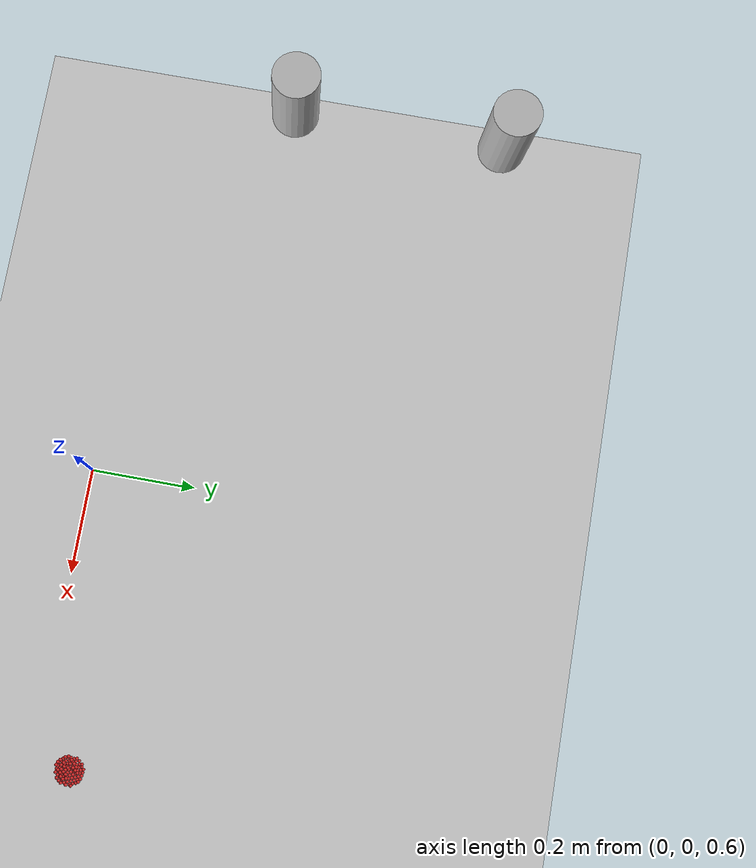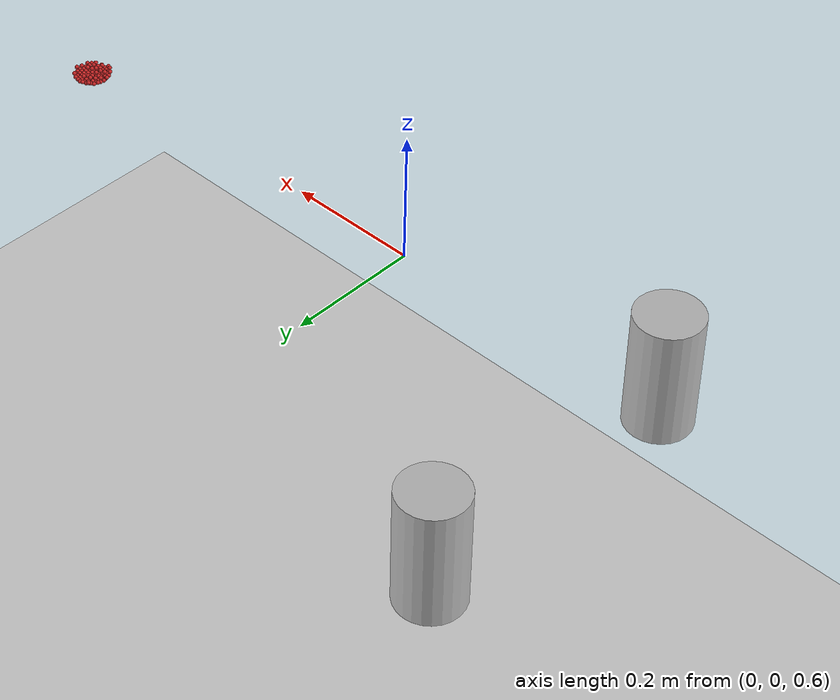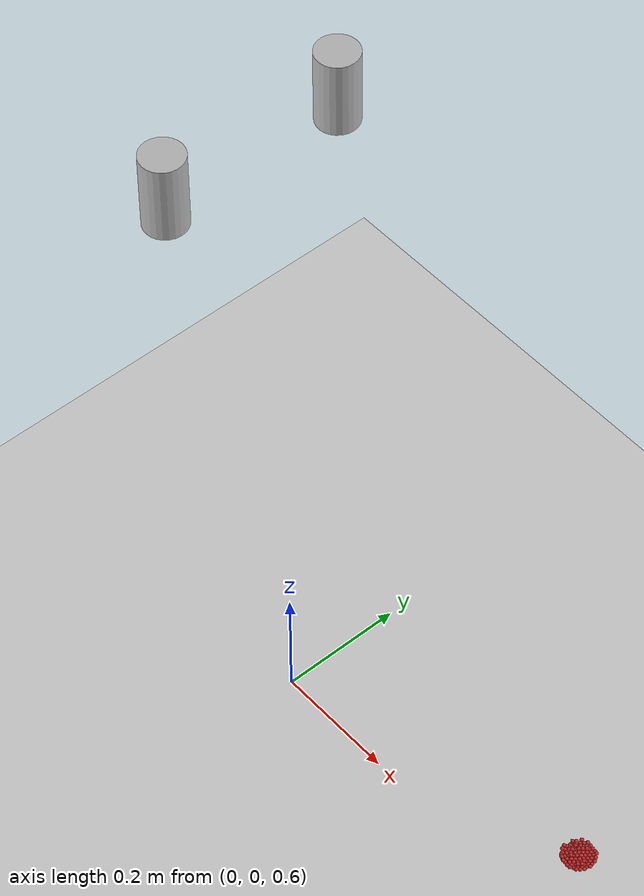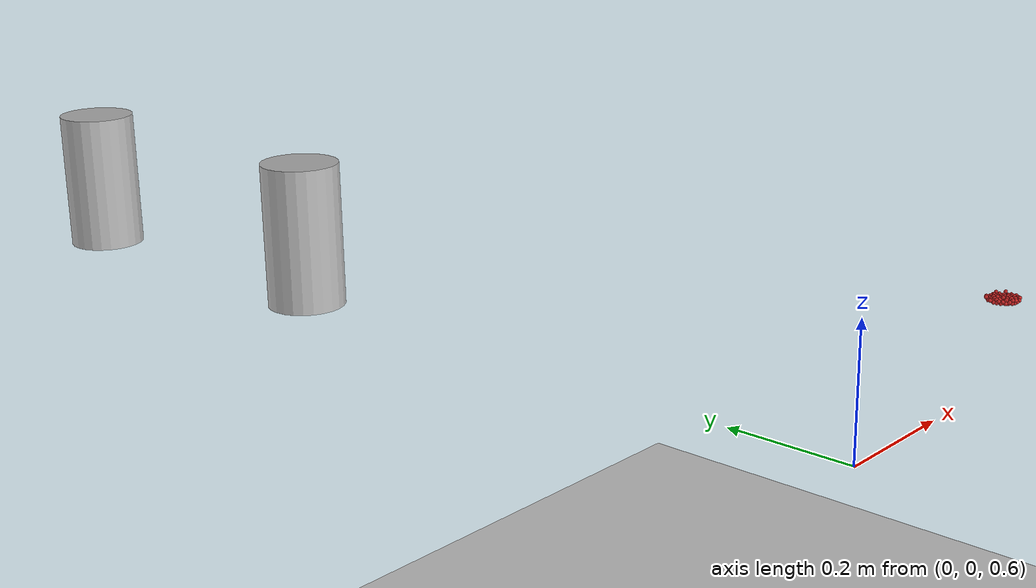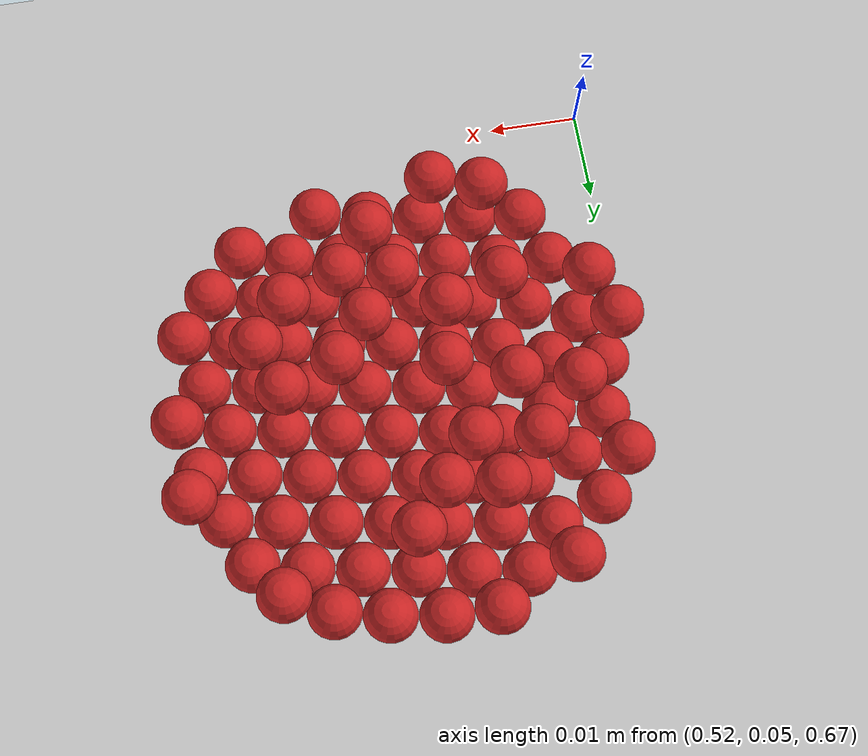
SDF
<sdf version="1.4">
 <world name="default">
  <physics type="ode">
   <gravity>0 0 -9.81</gravity>
   <ode>
    <solver><type>quick</type><iters>20</iters><sor>1</sor></solver>
    <constraints>
     <cfm>0</cfm>
     <erp>0.2</erp>
     <contact_max_correcting_vel>100</contact_max_correcting_vel>
     <contact_surface_layer>0</contact_surface_layer>
    </constraints>
   </ode>
   <real_time_update_rate>1000</real_time_update_rate>
   <max_step_size>0.001</max_step_size>
   <real_time_factor>1</real_time_factor>
  </physics>
  <light name="sun" type="directional">
   <pose>0 0 10 0 -0 0</pose>
   <diffuse>0.8 0.8 0.8 1</diffuse>
   <specular>0.2 0.2 0.2 1</specular>
   <attenuation>
    <range>1000</range>
    <constant>0.9</constant>
    <linear>0.01</linear>
    <quadratic>0.001</quadratic>
   </attenuation>
   <direction>-0.5 0.1 -0.9</direction>
  </light>
  <model name="ground_plane">
   <static>1</static>
   <link name="link">
    <collision name="collision">
     <geometry><plane><normal>0 0 1</normal><size>100 100</size></plane></geometry>
     <surface><friction><ode><mu>100</mu><mu2>50</mu2></ode></friction></surface>
    </collision>
    <visual name="visual">
     <cast_shadows>0</cast_shadows>
     <geometry><plane><normal>0 0 1</normal><size>100 100</size></plane></geometry>
     <material>
      <script><uri>file://media/materials/scripts/gazebo.material</uri><name>Gazebo/Grey</name></script>
     </material>
    </visual>
    <velocity_decay><linear>0</linear><angular>0</angular></velocity_decay>
   </link>
  </model>
  <scene><ambient>0.4 0.4 0.4 1</ambient><background>0.7 0.7 0.7 1</background><shadows>1</shadows></scene>
  <spherical_coordinates>
   <surface_model>EARTH_WGS84</surface_model>
   <latitude_deg>0</latitude_deg>
   <longitude_deg>0</longitude_deg>
   <elevation>0</elevation>
   <heading_deg>0</heading_deg>
  </spherical_coordinates>
  <model name="cocacola">
   <static>0</static>
   <link name="link">
    <inertial>
     <mass>0.25</mass>
     <inertia><ixx>0</ixx><ixy>0</ixy><ixz>0</ixz><iyy>0</iyy><iyz>0</iyz><izz>0</izz></inertia>
    </inertial>
    <collision name="collision">
     <pose>0 0 0.075 -3.14159 -0 0</pose>
     <geometry><cylinder><radius>0.04</radius><length>0.15</length></cylinder></geometry>
    </collision>
    <visual name="visual">
     <pose>0 0 0.075 -3.14159 -0 0</pose>
     <geometry><cylinder><radius>0.04</radius><length>0.15</length></cylinder></geometry>
     <material>
      <script>
       <uri>model://cocacola/material/scripts</uri>
       <uri>model://cocacola/material/textures</uri>
       <name>Custom/cocacola</name>
      </script>
     </material>
    </visual>
    <velocity_decay><linear>0</linear><angular>0</angular></velocity_decay>
   </link>
   <pose>-0.635135 0.281961 0.919998 8.8e-05 -0.000172 -0.00223</pose>
  </model>
  <model name="sprite">
   <static>0</static>
   <link name="link">
    <inertial>
     <mass>0.25</mass>
     <inertia><ixx>0</ixx><ixy>0</ixy><ixz>0</ixz><iyy>0</iyy><iyz>0</iyz><izz>0</izz></inertia>
    </inertial>
    <collision name="collision">
     <pose>0 0 0.075 -3.14159 -0 0</pose>
     <geometry><cylinder><radius>0.04</radius><length>0.15</length></cylinder></geometry>
    </collision>
    <visual name="visual">
     <pose>0 0 0.075 -3.14159 -0 0</pose>
     <geometry><cylinder><radius>0.04</radius><length>0.15</length></cylinder></geometry>
     <material>
      <script>
       <uri>model://sprite/material/scripts</uri>
       <uri>model://sprite/material/textures</uri>
       <name>Custom/sprite</name>
      </script>
     </material>
    </visual>
    <velocity_decay><linear>0</linear><angular>0</angular></velocity_decay>
   </link>
   <pose>-0.633912 0.639664 0.920008 0.000194 -7.8e-05 0.020234</pose>
  </model>
  <model name="sphere0">
   <pose>-0.001602 -0.00214 -0.026625 -0.000708 -0.001109 -1.3e-05</pose>
   <link name="link">
    <pose>0.534545 0.067517 0.694885 0 -0 0</pose>
    <inertial>
     <mass>1e-08</mass>
     <inertia><ixx>4e-08</ixx><ixy>0</ixy><ixz>0</ixz><iyy>4e-08</iyy><iyz>0</iyz><izz>4e-08</izz></inertia>
    </inertial>
    <collision name="collision">
     <surface>
      <bounce><restitution_coefficient>0.5</restitution_coefficient><threshold>0</threshold></bounce>
      <contact><ode><kp>1e+08</kp><kd>1</kd></ode></contact>
      <friction><ode><mu>1e-06</mu><mu2>1e-06</mu2></ode></friction>
     </surface>
     <geometry><sphere><radius>0.003</radius></sphere></geometry>
    </collision>
    <visual name="visual">
     <geometry><sphere><radius>0.003</radius></sphere></geometry>
     <material>
      <script><uri>file://media/materials/scripts/gazebo.material</uri><name>Gazebo/Red</name></script>
     </material>
    </visual>
    <velocity_decay><linear>0</linear><angular>0</angular></velocity_decay>
   </link>
   <static>0</static>
  </model>
  <model name="sphere1">
   <pose>0.000168 -0.008124 -0.026197 0.000256 -0.000729 0.000186</pose>
   <link name="link">
    <pose>0.540545 0.067517 0.694885 0 -0 0</pose>
    <inertial>
     <mass>1e-08</mass>
     <inertia><ixx>4e-08</ixx><ixy>0</ixy><ixz>0</ixz><iyy>4e-08</iyy><iyz>0</iyz><izz>4e-08</izz></inertia>
    </inertial>
    <collision name="collision">
     <surface>
      <bounce><restitution_coefficient>0.5</restitution_coefficient><threshold>0</threshold></bounce>
      <contact><ode><kp>1e+08</kp><kd>1</kd></ode></contact>
      <friction><ode><mu>1e-06</mu><mu2>1e-06</mu2></ode></friction>
     </surface>
     <geometry><sphere><radius>0.003</radius></sphere></geometry>
    </collision>
    <visual name="visual">
     <geometry><sphere><radius>0.003</radius></sphere></geometry>
     <material>
      <script><uri>file://media/materials/scripts/gazebo.material</uri><name>Gazebo/Red</name></script>
     </material>
    </visual>
    <velocity_decay><linear>0</linear><angular>0</angular></velocity_decay>
   </link>
   <static>0</static>
  </model>
  <model name="sphere2">
   <pose>0.003783 -0.004308 -0.026368 0.000322 -0.000606 -2.64698e-23</pose>
   <link name="link">
    <pose>0.546545 0.067517 0.694885 0 -0 0</pose>
    <inertial>
     <mass>1e-08</mass>
     <inertia><ixx>4e-08</ixx><ixy>0</ixy><ixz>0</ixz><iyy>4e-08</iyy><iyz>0</iyz><izz>4e-08</izz></inertia>
    </inertial>
    <collision name="collision">
     <surface>
      <bounce><restitution_coefficient>0.5</restitution_coefficient><threshold>0</threshold></bounce>
      <contact><ode><kp>1e+08</kp><kd>1</kd></ode></contact>
      <friction><ode><mu>1e-06</mu><mu2>1e-06</mu2></ode></friction>
     </surface>
     <geometry><sphere><radius>0.003</radius></sphere></geometry>
    </collision>
    <visual name="visual">
     <geometry><sphere><radius>0.003</radius></sphere></geometry>
     <material>
      <script><uri>file://media/materials/scripts/gazebo.material</uri><name>Gazebo/Red</name></script>
     </material>
    </visual>
    <velocity_decay><linear>0</linear><angular>0</angular></velocity_decay>
   </link>
   <static>0</static>
  </model>
  <model name="sphere3">
   <pose>0.012325 -0.001566 -0.023496 -0.000143 0.000357 -6e-05</pose>
   <link name="link">
    <pose>0.552545 0.067517 0.694885 0 -0 0</pose>
    <inertial>
     <mass>1e-08</mass>
     <inertia><ixx>4e-08</ixx><ixy>0</ixy><ixz>0</ixz><iyy>4e-08</iyy><iyz>0</iyz><izz>4e-08</izz></inertia>
    </inertial>
    <collision name="collision">
     <surface>
      <bounce><restitution_coefficient>0.5</restitution_coefficient><threshold>0</threshold></bounce>
      <contact><ode><kp>1e+08</kp><kd>1</kd></ode></contact>
      <friction><ode><mu>1e-06</mu><mu2>1e-06</mu2></ode></friction>
     </surface>
     <geometry><sphere><radius>0.003</radius></sphere></geometry>
    </collision>
    <visual name="visual">
     <geometry><sphere><radius>0.003</radius></sphere></geometry>
     <material>
      <script><uri>file://media/materials/scripts/gazebo.material</uri><name>Gazebo/Red</name></script>
     </material>
    </visual>
    <velocity_decay><linear>0</linear><angular>0</angular></velocity_decay>
   </link>
   <static>0</static>
  </model>
  <model name="sphere4">
   <pose>-0.004573 -0.00176 -0.026239 0.000105 -0.000252 -3.30872e-24</pose>
   <link name="link">
    <pose>0.534545 0.073517 0.694885 0 -0 0</pose>
    <inertial>
     <mass>1e-08</mass>
     <inertia><ixx>4e-08</ixx><ixy>0</ixy><ixz>0</ixz><iyy>4e-08</iyy><iyz>0</iyz><izz>4e-08</izz></inertia>
    </inertial>
    <collision name="collision">
     <surface>
      <bounce><restitution_coefficient>0.5</restitution_coefficient><threshold>0</threshold></bounce>
      <contact><ode><kp>1e+08</kp><kd>1</kd></ode></contact>
      <friction><ode><mu>1e-06</mu><mu2>1e-06</mu2></ode></friction>
     </surface>
     <geometry><sphere><radius>0.003</radius></sphere></geometry>
    </collision>
    <visual name="visual">
     <geometry><sphere><radius>0.003</radius></sphere></geometry>
     <material>
      <script><uri>file://media/materials/scripts/gazebo.material</uri><name>Gazebo/Red</name></script>
     </material>
    </visual>
    <velocity_decay><linear>0</linear><angular>0</angular></velocity_decay>
   </link>
   <static>0</static>
  </model>
  <model name="sphere5">
   <pose>-0.006587 0.002887 -0.026107 0.000405 -0.000181 0</pose>
   <link name="link">
    <pose>0.540545 0.073517 0.694885 0 -0 0</pose>
    <inertial>
     <mass>1e-08</mass>
     <inertia><ixx>4e-08</ixx><ixy>0</ixy><ixz>0</ixz><iyy>4e-08</iyy><iyz>0</iyz><izz>4e-08</izz></inertia>
    </inertial>
    <collision name="collision">
     <surface>
      <bounce><restitution_coefficient>0.5</restitution_coefficient><threshold>0</threshold></bounce>
      <contact><ode><kp>1e+08</kp><kd>1</kd></ode></contact>
      <friction><ode><mu>1e-06</mu><mu2>1e-06</mu2></ode></friction>
     </surface>
     <geometry><sphere><radius>0.003</radius></sphere></geometry>
    </collision>
    <visual name="visual">
     <geometry><sphere><radius>0.003</radius></sphere></geometry>
     <material>
      <script><uri>file://media/materials/scripts/gazebo.material</uri><name>Gazebo/Red</name></script>
     </material>
    </visual>
    <velocity_decay><linear>0</linear><angular>0</angular></velocity_decay>
   </link>
   <static>0</static>
  </model>
  <model name="sphere6">
   <pose>0.004831 -9.6e-05 -0.02579 0.00028 0.000304 0</pose>
   <link name="link">
    <pose>0.546545 0.073517 0.694885 0 -0 0</pose>
    <inertial>
     <mass>1e-08</mass>
     <inertia><ixx>4e-08</ixx><ixy>0</ixy><ixz>0</ixz><iyy>4e-08</iyy><iyz>0</iyz><izz>4e-08</izz></inertia>
    </inertial>
    <collision name="collision">
     <surface>
      <bounce><restitution_coefficient>0.5</restitution_coefficient><threshold>0</threshold></bounce>
      <contact><ode><kp>1e+08</kp><kd>1</kd></ode></contact>
      <friction><ode><mu>1e-06</mu><mu2>1e-06</mu2></ode></friction>
     </surface>
     <geometry><sphere><radius>0.003</radius></sphere></geometry>
    </collision>
    <visual name="visual">
     <geometry><sphere><radius>0.003</radius></sphere></geometry>
     <material>
      <script><uri>file://media/materials/scripts/gazebo.material</uri><name>Gazebo/Red</name></script>
     </material>
    </visual>
    <velocity_decay><linear>0</linear><angular>0</angular></velocity_decay>
   </link>
   <static>0</static>
  </model>
  <model name="sphere7">
   <pose>0.016099 -0.002313 -0.023103 8.5e-05 -6.7e-05 -0.000356</pose>
   <link name="link">
    <pose>0.552545 0.073517 0.694885 0 -0 0</pose>
    <inertial>
     <mass>1e-08</mass>
     <inertia><ixx>4e-08</ixx><ixy>0</ixy><ixz>0</ixz><iyy>4e-08</iyy><iyz>0</iyz><izz>4e-08</izz></inertia>
    </inertial>
    <collision name="collision">
     <surface>
      <bounce><restitution_coefficient>0.5</restitution_coefficient><threshold>0</threshold></bounce>
      <contact><ode><kp>1e+08</kp><kd>1</kd></ode></contact>
      <friction><ode><mu>1e-06</mu><mu2>1e-06</mu2></ode></friction>
     </surface>
     <geometry><sphere><radius>0.003</radius></sphere></geometry>
    </collision>
    <visual name="visual">
     <geometry><sphere><radius>0.003</radius></sphere></geometry>
     <material>
      <script><uri>file://media/materials/scripts/gazebo.material</uri><name>Gazebo/Red</name></script>
     </material>
    </visual>
    <velocity_decay><linear>0</linear><angular>0</angular></velocity_decay>
   </link>
   <static>0</static>
  </model>
  <model name="sphere8">
   <pose>-0.00674 0.010775 -0.026115 0.000196 -0.000248 -1e-06</pose>
   <link name="link">
    <pose>0.534545 0.079517 0.694885 0 -0 0</pose>
    <inertial>
     <mass>1e-08</mass>
     <inertia><ixx>4e-08</ixx><ixy>0</ixy><ixz>0</ixz><iyy>4e-08</iyy><iyz>0</iyz><izz>4e-08</izz></inertia>
    </inertial>
    <collision name="collision">
     <surface>
      <bounce><restitution_coefficient>0.5</restitution_coefficient><threshold>0</threshold></bounce>
      <contact><ode><kp>1e+08</kp><kd>1</kd></ode></contact>
      <friction><ode><mu>1e-06</mu><mu2>1e-06</mu2></ode></friction>
     </surface>
     <geometry><sphere><radius>0.003</radius></sphere></geometry>
    </collision>
    <visual name="visual">
     <geometry><sphere><radius>0.003</radius></sphere></geometry>
     <material>
      <script><uri>file://media/materials/scripts/gazebo.material</uri><name>Gazebo/Red</name></script>
     </material>
    </visual>
    <velocity_decay><linear>0</linear><angular>0</angular></velocity_decay>
   </link>
   <static>0</static>
  </model>
  <model name="sphere9">
   <pose>-0.00137 0.011253 -0.025864 -0.000341 0.000129 6.61744e-24</pose>
   <link name="link">
    <pose>0.540545 0.079517 0.694885 0 -0 0</pose>
    <inertial>
     <mass>1e-08</mass>
     <inertia><ixx>4e-08</ixx><ixy>0</ixy><ixz>0</ixz><iyy>4e-08</iyy><iyz>0</iyz><izz>4e-08</izz></inertia>
    </inertial>
    <collision name="collision">
     <surface>
      <bounce><restitution_coefficient>0.5</restitution_coefficient><threshold>0</threshold></bounce>
      <contact><ode><kp>1e+08</kp><kd>1</kd></ode></contact>
      <friction><ode><mu>1e-06</mu><mu2>1e-06</mu2></ode></friction>
     </surface>
     <geometry><sphere><radius>0.003</radius></sphere></geometry>
    </collision>
    <visual name="visual">
     <geometry><sphere><radius>0.003</radius></sphere></geometry>
     <material>
      <script><uri>file://media/materials/scripts/gazebo.material</uri><name>Gazebo/Red</name></script>
     </material>
    </visual>
    <velocity_decay><linear>0</linear><angular>0</angular></velocity_decay>
   </link>
   <static>0</static>
  </model>
  <model name="sphere10">
   <pose>-0.003062 0.000418 -0.02591 0.000197 7.5e-05 -1.65436e-24</pose>
   <link name="link">
    <pose>0.546545 0.079517 0.694885 0 -0 0</pose>
    <inertial>
     <mass>1e-08</mass>
     <inertia><ixx>4e-08</ixx><ixy>0</ixy><ixz>0</ixz><iyy>4e-08</iyy><iyz>0</iyz><izz>4e-08</izz></inertia>
    </inertial>
    <collision name="collision">
     <surface>
      <bounce><restitution_coefficient>0.5</restitution_coefficient><threshold>0</threshold></bounce>
      <contact><ode><kp>1e+08</kp><kd>1</kd></ode></contact>
      <friction><ode><mu>1e-06</mu><mu2>1e-06</mu2></ode></friction>
     </surface>
     <geometry><sphere><radius>0.003</radius></sphere></geometry>
    </collision>
    <visual name="visual">
     <geometry><sphere><radius>0.003</radius></sphere></geometry>
     <material>
      <script><uri>file://media/materials/scripts/gazebo.material</uri><name>Gazebo/Red</name></script>
     </material>
    </visual>
    <velocity_decay><linear>0</linear><angular>0</angular></velocity_decay>
   </link>
   <static>0</static>
  </model>
  <model name="sphere11">
   <pose>0.017049 0.010197 -0.02053 -0.000122 0.000524 4.7e-05</pose>
   <link name="link">
    <pose>0.552545 0.079517 0.694885 0 -0 0</pose>
    <inertial>
     <mass>1e-08</mass>
     <inertia><ixx>4e-08</ixx><ixy>0</ixy><ixz>0</ixz><iyy>4e-08</iyy><iyz>0</iyz><izz>4e-08</izz></inertia>
    </inertial>
    <collision name="collision">
     <surface>
      <bounce><restitution_coefficient>0.5</restitution_coefficient><threshold>0</threshold></bounce>
      <contact><ode><kp>1e+08</kp><kd>1</kd></ode></contact>
      <friction><ode><mu>1e-06</mu><mu2>1e-06</mu2></ode></friction>
     </surface>
     <geometry><sphere><radius>0.003</radius></sphere></geometry>
    </collision>
    <visual name="visual">
     <geometry><sphere><radius>0.003</radius></sphere></geometry>
     <material>
      <script><uri>file://media/materials/scripts/gazebo.material</uri><name>Gazebo/Red</name></script>
     </material>
    </visual>
    <velocity_decay><linear>0</linear><angular>0</angular></velocity_decay>
   </link>
   <static>0</static>
  </model>
  <model name="sphere12">
   <pose>0.000833 0.016596 -0.025909 -0.000255 -0.000506 -0.000117</pose>
   <link name="link">
    <pose>0.534545 0.085517 0.694885 0 -0 0</pose>
    <inertial>
     <mass>1e-08</mass>
     <inertia><ixx>4e-08</ixx><ixy>0</ixy><ixz>0</ixz><iyy>4e-08</iyy><iyz>0</iyz><izz>4e-08</izz></inertia>
    </inertial>
    <collision name="collision">
     <surface>
      <bounce><restitution_coefficient>0.5</restitution_coefficient><threshold>0</threshold></bounce>
      <contact><ode><kp>1e+08</kp><kd>1</kd></ode></contact>
      <friction><ode><mu>1e-06</mu><mu2>1e-06</mu2></ode></friction>
     </surface>
     <geometry><sphere><radius>0.003</radius></sphere></geometry>
    </collision>
    <visual name="visual">
     <geometry><sphere><radius>0.003</radius></sphere></geometry>
     <material>
      <script><uri>file://media/materials/scripts/gazebo.material</uri><name>Gazebo/Red</name></script>
     </material>
    </visual>
    <velocity_decay><linear>0</linear><angular>0</angular></velocity_decay>
   </link>
   <static>0</static>
  </model>
  <model name="sphere13">
   <pose>-0.001526 0.020282 -0.023391 -0.000414 -0.000174 0.000218</pose>
   <link name="link">
    <pose>0.540545 0.085517 0.694885 0 -0 0</pose>
    <inertial>
     <mass>1e-08</mass>
     <inertia><ixx>4e-08</ixx><ixy>0</ixy><ixz>0</ixz><iyy>4e-08</iyy><iyz>0</iyz><izz>4e-08</izz></inertia>
    </inertial>
    <collision name="collision">
     <surface>
      <bounce><restitution_coefficient>0.5</restitution_coefficient><threshold>0</threshold></bounce>
      <contact><ode><kp>1e+08</kp><kd>1</kd></ode></contact>
      <friction><ode><mu>1e-06</mu><mu2>1e-06</mu2></ode></friction>
     </surface>
     <geometry><sphere><radius>0.003</radius></sphere></geometry>
    </collision>
    <visual name="visual">
     <geometry><sphere><radius>0.003</radius></sphere></geometry>
     <material>
      <script><uri>file://media/materials/scripts/gazebo.material</uri><name>Gazebo/Red</name></script>
     </material>
    </visual>
    <velocity_decay><linear>0</linear><angular>0</angular></velocity_decay>
   </link>
   <static>0</static>
  </model>
  <model name="sphere14">
   <pose>0.010312 0.018721 -0.024799 0.000367 -0.000589 -0.000438</pose>
   <link name="link">
    <pose>0.546545 0.085517 0.694885 0 -0 0</pose>
    <inertial>
     <mass>1e-08</mass>
     <inertia><ixx>4e-08</ixx><ixy>0</ixy><ixz>0</ixz><iyy>4e-08</iyy><iyz>0</iyz><izz>4e-08</izz></inertia>
    </inertial>
    <collision name="collision">
     <surface>
      <bounce><restitution_coefficient>0.5</restitution_coefficient><threshold>0</threshold></bounce>
      <contact><ode><kp>1e+08</kp><kd>1</kd></ode></contact>
      <friction><ode><mu>1e-06</mu><mu2>1e-06</mu2></ode></friction>
     </surface>
     <geometry><sphere><radius>0.003</radius></sphere></geometry>
    </collision>
    <visual name="visual">
     <geometry><sphere><radius>0.003</radius></sphere></geometry>
     <material>
      <script><uri>file://media/materials/scripts/gazebo.material</uri><name>Gazebo/Red</name></script>
     </material>
    </visual>
    <velocity_decay><linear>0</linear><angular>0</angular></velocity_decay>
   </link>
   <static>0</static>
  </model>
  <model name="sphere15">
   <pose>0.008519 0.015651 -0.021432 -0.000885 0.000506 -0.000228</pose>
   <link name="link">
    <pose>0.552545 0.085517 0.694885 0 -0 0</pose>
    <inertial>
     <mass>1e-08</mass>
     <inertia><ixx>4e-08</ixx><ixy>0</ixy><ixz>0</ixz><iyy>4e-08</iyy><iyz>0</iyz><izz>4e-08</izz></inertia>
    </inertial>
    <collision name="collision">
     <surface>
      <bounce><restitution_coefficient>0.5</restitution_coefficient><threshold>0</threshold></bounce>
      <contact><ode><kp>1e+08</kp><kd>1</kd></ode></contact>
      <friction><ode><mu>1e-06</mu><mu2>1e-06</mu2></ode></friction>
     </surface>
     <geometry><sphere><radius>0.003</radius></sphere></geometry>
    </collision>
    <visual name="visual">
     <geometry><sphere><radius>0.003</radius></sphere></geometry>
     <material>
      <script><uri>file://media/materials/scripts/gazebo.material</uri><name>Gazebo/Red</name></script>
     </material>
    </visual>
    <velocity_decay><linear>0</linear><angular>0</angular></velocity_decay>
   </link>
   <static>0</static>
  </model>
  <model name="sphere16">
   <pose>-0.008166 0.000151 -0.031257 0.000916 -9.1e-05 -0.000279</pose>
   <link name="link">
    <pose>0.534545 0.067517 0.700885 0 -0 0</pose>
    <inertial>
     <mass>1e-08</mass>
     <inertia><ixx>4e-08</ixx><ixy>0</ixy><ixz>0</ixz><iyy>4e-08</iyy><iyz>0</iyz><izz>4e-08</izz></inertia>
    </inertial>
    <collision name="collision">
     <surface>
      <bounce><restitution_coefficient>0.5</restitution_coefficient><threshold>0</threshold></bounce>
      <contact><ode><kp>1e+08</kp><kd>1</kd></ode></contact>
      <friction><ode><mu>1e-06</mu><mu2>1e-06</mu2></ode></friction>
     </surface>
     <geometry><sphere><radius>0.003</radius></sphere></geometry>
    </collision>
    <visual name="visual">
     <geometry><sphere><radius>0.003</radius></sphere></geometry>
     <material>
      <script><uri>file://media/materials/scripts/gazebo.material</uri><name>Gazebo/Red</name></script>
     </material>
    </visual>
    <velocity_decay><linear>0</linear><angular>0</angular></velocity_decay>
   </link>
   <static>0</static>
  </model>
  <model name="sphere17">
   <pose>-0.001929 -0.010718 -0.02668 0.000136 -0.000102 0.000212</pose>
   <link name="link">
    <pose>0.540545 0.067517 0.700885 0 -0 0</pose>
    <inertial>
     <mass>1e-08</mass>
     <inertia><ixx>4e-08</ixx><ixy>0</ixy><ixz>0</ixz><iyy>4e-08</iyy><iyz>0</iyz><izz>4e-08</izz></inertia>
    </inertial>
    <collision name="collision">
     <surface>
      <bounce><restitution_coefficient>0.5</restitution_coefficient><threshold>0</threshold></bounce>
      <contact><ode><kp>1e+08</kp><kd>1</kd></ode></contact>
      <friction><ode><mu>1e-06</mu><mu2>1e-06</mu2></ode></friction>
     </surface>
     <geometry><sphere><radius>0.003</radius></sphere></geometry>
    </collision>
    <visual name="visual">
     <geometry><sphere><radius>0.003</radius></sphere></geometry>
     <material>
      <script><uri>file://media/materials/scripts/gazebo.material</uri><name>Gazebo/Red</name></script>
     </material>
    </visual>
    <velocity_decay><linear>0</linear><angular>0</angular></velocity_decay>
   </link>
   <static>0</static>
  </model>
  <model name="sphere18">
   <pose>-0.000647 -0.009367 -0.031409 -0.000324 0.000296 -7.7e-05</pose>
   <link name="link">
    <pose>0.546545 0.067517 0.700885 0 -0 0</pose>
    <inertial>
     <mass>1e-08</mass>
     <inertia><ixx>4e-08</ixx><ixy>0</ixy><ixz>0</ixz><iyy>4e-08</iyy><iyz>0</iyz><izz>4e-08</izz></inertia>
    </inertial>
    <collision name="collision">
     <surface>
      <bounce><restitution_coefficient>0.5</restitution_coefficient><threshold>0</threshold></bounce>
      <contact><ode><kp>1e+08</kp><kd>1</kd></ode></contact>
      <friction><ode><mu>1e-06</mu><mu2>1e-06</mu2></ode></friction>
     </surface>
     <geometry><sphere><radius>0.003</radius></sphere></geometry>
    </collision>
    <visual name="visual">
     <geometry><sphere><radius>0.003</radius></sphere></geometry>
     <material>
      <script><uri>file://media/materials/scripts/gazebo.material</uri><name>Gazebo/Red</name></script>
     </material>
    </visual>
    <velocity_decay><linear>0</linear><angular>0</angular></velocity_decay>
   </link>
   <static>0</static>
  </model>
  <model name="sphere19">
   <pose>0.003403 -0.00545 -0.032095 8.1e-05 -0.000187 -2.3e-05</pose>
   <link name="link">
    <pose>0.552545 0.067517 0.700885 0 -0 0</pose>
    <inertial>
     <mass>1e-08</mass>
     <inertia><ixx>4e-08</ixx><ixy>0</ixy><ixz>0</ixz><iyy>4e-08</iyy><iyz>0</iyz><izz>4e-08</izz></inertia>
    </inertial>
    <collision name="collision">
     <surface>
      <bounce><restitution_coefficient>0.5</restitution_coefficient><threshold>0</threshold></bounce>
      <contact><ode><kp>1e+08</kp><kd>1</kd></ode></contact>
      <friction><ode><mu>1e-06</mu><mu2>1e-06</mu2></ode></friction>
     </surface>
     <geometry><sphere><radius>0.003</radius></sphere></geometry>
    </collision>
    <visual name="visual">
     <geometry><sphere><radius>0.003</radius></sphere></geometry>
     <material>
      <script><uri>file://media/materials/scripts/gazebo.material</uri><name>Gazebo/Red</name></script>
     </material>
    </visual>
    <velocity_decay><linear>0</linear><angular>0</angular></velocity_decay>
   </link>
   <static>0</static>
  </model>
  <model name="sphere20">
   <pose>-0.009894 0.000147 -0.03225 -0.000743 -0.000452 -3e-05</pose>
   <link name="link">
    <pose>0.534545 0.073517 0.700885 0 -0 0</pose>
    <inertial>
     <mass>1e-08</mass>
     <inertia><ixx>4e-08</ixx><ixy>0</ixy><ixz>0</ixz><iyy>4e-08</iyy><iyz>0</iyz><izz>4e-08</izz></inertia>
    </inertial>
    <collision name="collision">
     <surface>
      <bounce><restitution_coefficient>0.5</restitution_coefficient><threshold>0</threshold></bounce>
      <contact><ode><kp>1e+08</kp><kd>1</kd></ode></contact>
      <friction><ode><mu>1e-06</mu><mu2>1e-06</mu2></ode></friction>
     </surface>
     <geometry><sphere><radius>0.003</radius></sphere></geometry>
    </collision>
    <visual name="visual">
     <geometry><sphere><radius>0.003</radius></sphere></geometry>
     <material>
      <script><uri>file://media/materials/scripts/gazebo.material</uri><name>Gazebo/Red</name></script>
     </material>
    </visual>
    <velocity_decay><linear>0</linear><angular>0</angular></velocity_decay>
   </link>
   <static>0</static>
  </model>
  <model name="sphere21">
   <pose>-0.004246 -0.003203 -0.032221 -0.000283 -0.00048 -2.64698e-23</pose>
   <link name="link">
    <pose>0.540545 0.073517 0.700885 0 -0 0</pose>
    <inertial>
     <mass>1e-08</mass>
     <inertia><ixx>4e-08</ixx><ixy>0</ixy><ixz>0</ixz><iyy>4e-08</iyy><iyz>0</iyz><izz>4e-08</izz></inertia>
    </inertial>
    <collision name="collision">
     <surface>
      <bounce><restitution_coefficient>0.5</restitution_coefficient><threshold>0</threshold></bounce>
      <contact><ode><kp>1e+08</kp><kd>1</kd></ode></contact>
      <friction><ode><mu>1e-06</mu><mu2>1e-06</mu2></ode></friction>
     </surface>
     <geometry><sphere><radius>0.003</radius></sphere></geometry>
    </collision>
    <visual name="visual">
     <geometry><sphere><radius>0.003</radius></sphere></geometry>
     <material>
      <script><uri>file://media/materials/scripts/gazebo.material</uri><name>Gazebo/Red</name></script>
     </material>
    </visual>
    <velocity_decay><linear>0</linear><angular>0</angular></velocity_decay>
   </link>
   <static>0</static>
  </model>
  <model name="sphere22">
   <pose>-0.002006 -0.009545 -0.032442 4.9e-05 -0.000792 6.61745e-24</pose>
   <link name="link">
    <pose>0.546545 0.073517 0.700885 0 -0 0</pose>
    <inertial>
     <mass>1e-08</mass>
     <inertia><ixx>4e-08</ixx><ixy>0</ixy><ixz>0</ixz><iyy>4e-08</iyy><iyz>0</iyz><izz>4e-08</izz></inertia>
    </inertial>
    <collision name="collision">
     <surface>
      <bounce><restitution_coefficient>0.5</restitution_coefficient><threshold>0</threshold></bounce>
      <contact><ode><kp>1e+08</kp><kd>1</kd></ode></contact>
      <friction><ode><mu>1e-06</mu><mu2>1e-06</mu2></ode></friction>
     </surface>
     <geometry><sphere><radius>0.003</radius></sphere></geometry>
    </collision>
    <visual name="visual">
     <geometry><sphere><radius>0.003</radius></sphere></geometry>
     <material>
      <script><uri>file://media/materials/scripts/gazebo.material</uri><name>Gazebo/Red</name></script>
     </material>
    </visual>
    <velocity_decay><linear>0</linear><angular>0</angular></velocity_decay>
   </link>
   <static>0</static>
  </model>
  <model name="sphere23">
   <pose>0.010411 -0.002792 -0.031521 -0.000836 0.000662 9e-06</pose>
   <link name="link">
    <pose>0.552545 0.073517 0.700885 0 -0 0</pose>
    <inertial>
     <mass>1e-08</mass>
     <inertia><ixx>4e-08</ixx><ixy>0</ixy><ixz>0</ixz><iyy>4e-08</iyy><iyz>0</iyz><izz>4e-08</izz></inertia>
    </inertial>
    <collision name="collision">
     <surface>
      <bounce><restitution_coefficient>0.5</restitution_coefficient><threshold>0</threshold></bounce>
      <contact><ode><kp>1e+08</kp><kd>1</kd></ode></contact>
      <friction><ode><mu>1e-06</mu><mu2>1e-06</mu2></ode></friction>
     </surface>
     <geometry><sphere><radius>0.003</radius></sphere></geometry>
    </collision>
    <visual name="visual">
     <geometry><sphere><radius>0.003</radius></sphere></geometry>
     <material>
      <script><uri>file://media/materials/scripts/gazebo.material</uri><name>Gazebo/Red</name></script>
     </material>
    </visual>
    <velocity_decay><linear>0</linear><angular>0</angular></velocity_decay>
   </link>
   <static>0</static>
  </model>
  <model name="sphere24">
   <pose>-0.011701 0.000533 -0.03202 0.00018 -0.000489 -0.000103</pose>
   <link name="link">
    <pose>0.534545 0.079517 0.700885 0 -0 0</pose>
    <inertial>
     <mass>1e-08</mass>
     <inertia><ixx>4e-08</ixx><ixy>0</ixy><ixz>0</ixz><iyy>4e-08</iyy><iyz>0</iyz><izz>4e-08</izz></inertia>
    </inertial>
    <collision name="collision">
     <surface>
      <bounce><restitution_coefficient>0.5</restitution_coefficient><threshold>0</threshold></bounce>
      <contact><ode><kp>1e+08</kp><kd>1</kd></ode></contact>
      <friction><ode><mu>1e-06</mu><mu2>1e-06</mu2></ode></friction>
     </surface>
     <geometry><sphere><radius>0.003</radius></sphere></geometry>
    </collision>
    <visual name="visual">
     <geometry><sphere><radius>0.003</radius></sphere></geometry>
     <material>
      <script><uri>file://media/materials/scripts/gazebo.material</uri><name>Gazebo/Red</name></script>
     </material>
    </visual>
    <velocity_decay><linear>0</linear><angular>0</angular></velocity_decay>
   </link>
   <static>0</static>
  </model>
  <model name="sphere25">
   <pose>-0.01209 -0.001053 -0.032008 -0.000205 -0.000119 0</pose>
   <link name="link">
    <pose>0.540545 0.079517 0.700885 0 -0 0</pose>
    <inertial>
     <mass>1e-08</mass>
     <inertia><ixx>4e-08</ixx><ixy>0</ixy><ixz>0</ixz><iyy>4e-08</iyy><iyz>0</iyz><izz>4e-08</izz></inertia>
    </inertial>
    <collision name="collision">
     <surface>
      <bounce><restitution_coefficient>0.5</restitution_coefficient><threshold>0</threshold></bounce>
      <contact><ode><kp>1e+08</kp><kd>1</kd></ode></contact>
      <friction><ode><mu>1e-06</mu><mu2>1e-06</mu2></ode></friction>
     </surface>
     <geometry><sphere><radius>0.003</radius></sphere></geometry>
    </collision>
    <visual name="visual">
     <geometry><sphere><radius>0.003</radius></sphere></geometry>
     <material>
      <script><uri>file://media/materials/scripts/gazebo.material</uri><name>Gazebo/Red</name></script>
     </material>
    </visual>
    <velocity_decay><linear>0</linear><angular>0</angular></velocity_decay>
   </link>
   <static>0</static>
  </model>
  <model name="sphere26">
   <pose>0.006231 0.004149 -0.031625 0.000276 0.000655 0</pose>
   <link name="link">
    <pose>0.546545 0.079517 0.700885 0 -0 0</pose>
    <inertial>
     <mass>1e-08</mass>
     <inertia><ixx>4e-08</ixx><ixy>0</ixy><ixz>0</ixz><iyy>4e-08</iyy><iyz>0</iyz><izz>4e-08</izz></inertia>
    </inertial>
    <collision name="collision">
     <surface>
      <bounce><restitution_coefficient>0.5</restitution_coefficient><threshold>0</threshold></bounce>
      <contact><ode><kp>1e+08</kp><kd>1</kd></ode></contact>
      <friction><ode><mu>1e-06</mu><mu2>1e-06</mu2></ode></friction>
     </surface>
     <geometry><sphere><radius>0.003</radius></sphere></geometry>
    </collision>
    <visual name="visual">
     <geometry><sphere><radius>0.003</radius></sphere></geometry>
     <material>
      <script><uri>file://media/materials/scripts/gazebo.material</uri><name>Gazebo/Red</name></script>
     </material>
    </visual>
    <velocity_decay><linear>0</linear><angular>0</angular></velocity_decay>
   </link>
   <static>0</static>
  </model>
  <model name="sphere27">
   <pose>0.012449 0.001611 -0.031825 -0.000596 0.000119 1.1e-05</pose>
   <link name="link">
    <pose>0.552545 0.079517 0.700885 0 -0 0</pose>
    <inertial>
     <mass>1e-08</mass>
     <inertia><ixx>4e-08</ixx><ixy>0</ixy><ixz>0</ixz><iyy>4e-08</iyy><iyz>0</iyz><izz>4e-08</izz></inertia>
    </inertial>
    <collision name="collision">
     <surface>
      <bounce><restitution_coefficient>0.5</restitution_coefficient><threshold>0</threshold></bounce>
      <contact><ode><kp>1e+08</kp><kd>1</kd></ode></contact>
      <friction><ode><mu>1e-06</mu><mu2>1e-06</mu2></ode></friction>
     </surface>
     <geometry><sphere><radius>0.003</radius></sphere></geometry>
    </collision>
    <visual name="visual">
     <geometry><sphere><radius>0.003</radius></sphere></geometry>
     <material>
      <script><uri>file://media/materials/scripts/gazebo.material</uri><name>Gazebo/Red</name></script>
     </material>
    </visual>
    <velocity_decay><linear>0</linear><angular>0</angular></velocity_decay>
   </link>
   <static>0</static>
  </model>
  <model name="sphere28">
   <pose>-0.011848 0.006001 -0.030007 0.000122 -0.000795 -0.000744</pose>
   <link name="link">
    <pose>0.534545 0.085517 0.700885 0 -0 0</pose>
    <inertial>
     <mass>1e-08</mass>
     <inertia><ixx>4e-08</ixx><ixy>0</ixy><ixz>0</ixz><iyy>4e-08</iyy><iyz>0</iyz><izz>4e-08</izz></inertia>
    </inertial>
    <collision name="collision">
     <surface>
      <bounce><restitution_coefficient>0.5</restitution_coefficient><threshold>0</threshold></bounce>
      <contact><ode><kp>1e+08</kp><kd>1</kd></ode></contact>
      <friction><ode><mu>1e-06</mu><mu2>1e-06</mu2></ode></friction>
     </surface>
     <geometry><sphere><radius>0.003</radius></sphere></geometry>
    </collision>
    <visual name="visual">
     <geometry><sphere><radius>0.003</radius></sphere></geometry>
     <material>
      <script><uri>file://media/materials/scripts/gazebo.material</uri><name>Gazebo/Red</name></script>
     </material>
    </visual>
    <velocity_decay><linear>0</linear><angular>0</angular></velocity_decay>
   </link>
   <static>0</static>
  </model>
  <model name="sphere29">
   <pose>-0.00859 0.012608 -0.032571 0.000779 -0.001002 6e-06</pose>
   <link name="link">
    <pose>0.540545 0.085517 0.700885 0 -0 0</pose>
    <inertial>
     <mass>1e-08</mass>
     <inertia><ixx>4e-08</ixx><ixy>0</ixy><ixz>0</ixz><iyy>4e-08</iyy><iyz>0</iyz><izz>4e-08</izz></inertia>
    </inertial>
    <collision name="collision">
     <surface>
      <bounce><restitution_coefficient>0.5</restitution_coefficient><threshold>0</threshold></bounce>
      <contact><ode><kp>1e+08</kp><kd>1</kd></ode></contact>
      <friction><ode><mu>1e-06</mu><mu2>1e-06</mu2></ode></friction>
     </surface>
     <geometry><sphere><radius>0.003</radius></sphere></geometry>
    </collision>
    <visual name="visual">
     <geometry><sphere><radius>0.003</radius></sphere></geometry>
     <material>
      <script><uri>file://media/materials/scripts/gazebo.material</uri><name>Gazebo/Red</name></script>
     </material>
    </visual>
    <velocity_decay><linear>0</linear><angular>0</angular></velocity_decay>
   </link>
   <static>0</static>
  </model>
  <model name="sphere30">
   <pose>-2e-05 0.014712 -0.031812 -0.000101 0.000457 -1e-05</pose>
   <link name="link">
    <pose>0.546545 0.085517 0.700885 0 -0 0</pose>
    <inertial>
     <mass>1e-08</mass>
     <inertia><ixx>4e-08</ixx><ixy>0</ixy><ixz>0</ixz><iyy>4e-08</iyy><iyz>0</iyz><izz>4e-08</izz></inertia>
    </inertial>
    <collision name="collision">
     <surface>
      <bounce><restitution_coefficient>0.5</restitution_coefficient><threshold>0</threshold></bounce>
      <contact><ode><kp>1e+08</kp><kd>1</kd></ode></contact>
      <friction><ode><mu>1e-06</mu><mu2>1e-06</mu2></ode></friction>
     </surface>
     <geometry><sphere><radius>0.003</radius></sphere></geometry>
    </collision>
    <visual name="visual">
     <geometry><sphere><radius>0.003</radius></sphere></geometry>
     <material>
      <script><uri>file://media/materials/scripts/gazebo.material</uri><name>Gazebo/Red</name></script>
     </material>
    </visual>
    <velocity_decay><linear>0</linear><angular>0</angular></velocity_decay>
   </link>
   <static>0</static>
  </model>
  <model name="sphere31">
   <pose>0.008376 0.006946 -0.032013 -0.000408 -0.000157 0</pose>
   <link name="link">
    <pose>0.552545 0.085517 0.700885 0 -0 0</pose>
    <inertial>
     <mass>1e-08</mass>
     <inertia><ixx>4e-08</ixx><ixy>0</ixy><ixz>0</ixz><iyy>4e-08</iyy><iyz>0</iyz><izz>4e-08</izz></inertia>
    </inertial>
    <collision name="collision">
     <surface>
      <bounce><restitution_coefficient>0.5</restitution_coefficient><threshold>0</threshold></bounce>
      <contact><ode><kp>1e+08</kp><kd>1</kd></ode></contact>
      <friction><ode><mu>1e-06</mu><mu2>1e-06</mu2></ode></friction>
     </surface>
     <geometry><sphere><radius>0.003</radius></sphere></geometry>
    </collision>
    <visual name="visual">
     <geometry><sphere><radius>0.003</radius></sphere></geometry>
     <material>
      <script><uri>file://media/materials/scripts/gazebo.material</uri><name>Gazebo/Red</name></script>
     </material>
    </visual>
    <velocity_decay><linear>0</linear><angular>0</angular></velocity_decay>
   </link>
   <static>0</static>
  </model>
  <model name="sphere32">
   <pose>-0.000154 -0.006746 -0.03734 0.000604 -0.00014 -5.2e-05</pose>
   <link name="link">
    <pose>0.534545 0.067517 0.706885 0 -0 0</pose>
    <inertial>
     <mass>1e-08</mass>
     <inertia><ixx>4e-08</ixx><ixy>0</ixy><ixz>0</ixz><iyy>4e-08</iyy><iyz>0</iyz><izz>4e-08</izz></inertia>
    </inertial>
    <collision name="collision">
     <surface>
      <bounce><restitution_coefficient>0.5</restitution_coefficient><threshold>0</threshold></bounce>
      <contact><ode><kp>1e+08</kp><kd>1</kd></ode></contact>
      <friction><ode><mu>1e-06</mu><mu2>1e-06</mu2></ode></friction>
     </surface>
     <geometry><sphere><radius>0.003</radius></sphere></geometry>
    </collision>
    <visual name="visual">
     <geometry><sphere><radius>0.003</radius></sphere></geometry>
     <material>
      <script><uri>file://media/materials/scripts/gazebo.material</uri><name>Gazebo/Red</name></script>
     </material>
    </visual>
    <velocity_decay><linear>0</linear><angular>0</angular></velocity_decay>
   </link>
   <static>0</static>
  </model>
  <model name="sphere33">
   <pose>0.006077 -0.005772 -0.032692 0 -0 0</pose>
   <link name="link">
    <pose>0.540545 0.067517 0.706885 0 -0 0</pose>
    <inertial>
     <mass>1e-08</mass>
     <inertia><ixx>4e-08</ixx><ixy>0</ixy><ixz>0</ixz><iyy>4e-08</iyy><iyz>0</iyz><izz>4e-08</izz></inertia>
    </inertial>
    <collision name="collision">
     <surface>
      <bounce><restitution_coefficient>0.5</restitution_coefficient><threshold>0</threshold></bounce>
      <contact><ode><kp>1e+08</kp><kd>1</kd></ode></contact>
      <friction><ode><mu>1e-06</mu><mu2>1e-06</mu2></ode></friction>
     </surface>
     <geometry><sphere><radius>0.003</radius></sphere></geometry>
    </collision>
    <visual name="visual">
     <geometry><sphere><radius>0.003</radius></sphere></geometry>
     <material>
      <script><uri>file://media/materials/scripts/gazebo.material</uri><name>Gazebo/Red</name></script>
     </material>
    </visual>
    <velocity_decay><linear>0</linear><angular>0</angular></velocity_decay>
   </link>
   <static>0</static>
  </model>
  <model name="sphere34">
   <pose>0.007107 0.000179 -0.037913 0.000113 8.3e-05 -3e-06</pose>
   <link name="link">
    <pose>0.546545 0.067517 0.706885 0 -0 0</pose>
    <inertial>
     <mass>1e-08</mass>
     <inertia><ixx>4e-08</ixx><ixy>0</ixy><ixz>0</ixz><iyy>4e-08</iyy><iyz>0</iyz><izz>4e-08</izz></inertia>
    </inertial>
    <collision name="collision">
     <surface>
      <bounce><restitution_coefficient>0.5</restitution_coefficient><threshold>0</threshold></bounce>
      <contact><ode><kp>1e+08</kp><kd>1</kd></ode></contact>
      <friction><ode><mu>1e-06</mu><mu2>1e-06</mu2></ode></friction>
     </surface>
     <geometry><sphere><radius>0.003</radius></sphere></geometry>
    </collision>
    <visual name="visual">
     <geometry><sphere><radius>0.003</radius></sphere></geometry>
     <material>
      <script><uri>file://media/materials/scripts/gazebo.material</uri><name>Gazebo/Red</name></script>
     </material>
    </visual>
    <velocity_decay><linear>0</linear><angular>0</angular></velocity_decay>
   </link>
   <static>0</static>
  </model>
  <model name="sphere35">
   <pose>0.008203 0.005987 -0.033085 0 -0 0</pose>
   <link name="link">
    <pose>0.552545 0.067517 0.706885 0 -0 0</pose>
    <inertial>
     <mass>1e-08</mass>
     <inertia><ixx>4e-08</ixx><ixy>0</ixy><ixz>0</ixz><iyy>4e-08</iyy><iyz>0</iyz><izz>4e-08</izz></inertia>
    </inertial>
    <collision name="collision">
     <surface>
      <bounce><restitution_coefficient>0.5</restitution_coefficient><threshold>0</threshold></bounce>
      <contact><ode><kp>1e+08</kp><kd>1</kd></ode></contact>
      <friction><ode><mu>1e-06</mu><mu2>1e-06</mu2></ode></friction>
     </surface>
     <geometry><sphere><radius>0.003</radius></sphere></geometry>
    </collision>
    <visual name="visual">
     <geometry><sphere><radius>0.003</radius></sphere></geometry>
     <material>
      <script><uri>file://media/materials/scripts/gazebo.material</uri><name>Gazebo/Red</name></script>
     </material>
    </visual>
    <velocity_decay><linear>0</linear><angular>0</angular></velocity_decay>
   </link>
   <static>0</static>
  </model>
  <model name="sphere36">
   <pose>-0.004866 0.011164 -0.038175 0.000272 -0.000185 0</pose>
   <link name="link">
    <pose>0.534545 0.073517 0.706885 0 -0 0</pose>
    <inertial>
     <mass>1e-08</mass>
     <inertia><ixx>4e-08</ixx><ixy>0</ixy><ixz>0</ixz><iyy>4e-08</iyy><iyz>0</iyz><izz>4e-08</izz></inertia>
    </inertial>
    <collision name="collision">
     <surface>
      <bounce><restitution_coefficient>0.5</restitution_coefficient><threshold>0</threshold></bounce>
      <contact><ode><kp>1e+08</kp><kd>1</kd></ode></contact>
      <friction><ode><mu>1e-06</mu><mu2>1e-06</mu2></ode></friction>
     </surface>
     <geometry><sphere><radius>0.003</radius></sphere></geometry>
    </collision>
    <visual name="visual">
     <geometry><sphere><radius>0.003</radius></sphere></geometry>
     <material>
      <script><uri>file://media/materials/scripts/gazebo.material</uri><name>Gazebo/Red</name></script>
     </material>
    </visual>
    <velocity_decay><linear>0</linear><angular>0</angular></velocity_decay>
   </link>
   <static>0</static>
  </model>
  <model name="sphere37">
   <pose>-0.002943 0.00741 -0.037958 0.000232 -5e-06 0</pose>
   <link name="link">
    <pose>0.540545 0.073517 0.706885 0 -0 0</pose>
    <inertial>
     <mass>1e-08</mass>
     <inertia><ixx>4e-08</ixx><ixy>0</ixy><ixz>0</ixz><iyy>4e-08</iyy><iyz>0</iyz><izz>4e-08</izz></inertia>
    </inertial>
    <collision name="collision">
     <surface>
      <bounce><restitution_coefficient>0.5</restitution_coefficient><threshold>0</threshold></bounce>
      <contact><ode><kp>1e+08</kp><kd>1</kd></ode></contact>
      <friction><ode><mu>1e-06</mu><mu2>1e-06</mu2></ode></friction>
     </surface>
     <geometry><sphere><radius>0.003</radius></sphere></geometry>
    </collision>
    <visual name="visual">
     <geometry><sphere><radius>0.003</radius></sphere></geometry>
     <material>
      <script><uri>file://media/materials/scripts/gazebo.material</uri><name>Gazebo/Red</name></script>
     </material>
    </visual>
    <velocity_decay><linear>0</linear><angular>0</angular></velocity_decay>
   </link>
   <static>0</static>
  </model>
  <model name="sphere38">
   <pose>0.008831 0.004468 -0.037978 0.000169 -2e-05 0</pose>
   <link name="link">
    <pose>0.546545 0.073517 0.706885 0 -0 0</pose>
    <inertial>
     <mass>1e-08</mass>
     <inertia><ixx>4e-08</ixx><ixy>0</ixy><ixz>0</ixz><iyy>4e-08</iyy><iyz>0</iyz><izz>4e-08</izz></inertia>
    </inertial>
    <collision name="collision">
     <surface>
      <bounce><restitution_coefficient>0.5</restitution_coefficient><threshold>0</threshold></bounce>
      <contact><ode><kp>1e+08</kp><kd>1</kd></ode></contact>
      <friction><ode><mu>1e-06</mu><mu2>1e-06</mu2></ode></friction>
     </surface>
     <geometry><sphere><radius>0.003</radius></sphere></geometry>
    </collision>
    <visual name="visual">
     <geometry><sphere><radius>0.003</radius></sphere></geometry>
     <material>
      <script><uri>file://media/materials/scripts/gazebo.material</uri><name>Gazebo/Red</name></script>
     </material>
    </visual>
    <velocity_decay><linear>0</linear><angular>0</angular></velocity_decay>
   </link>
   <static>0</static>
  </model>
  <model name="sphere39">
   <pose>0.014796 0.002671 -0.038138 0.000351 -0.000175 1.1e-05</pose>
   <link name="link">
    <pose>0.552545 0.073517 0.706885 0 -0 0</pose>
    <inertial>
     <mass>1e-08</mass>
     <inertia><ixx>4e-08</ixx><ixy>0</ixy><ixz>0</ixz><iyy>4e-08</iyy><iyz>0</iyz><izz>4e-08</izz></inertia>
    </inertial>
    <collision name="collision">
     <surface>
      <bounce><restitution_coefficient>0.5</restitution_coefficient><threshold>0</threshold></bounce>
      <contact><ode><kp>1e+08</kp><kd>1</kd></ode></contact>
      <friction><ode><mu>1e-06</mu><mu2>1e-06</mu2></ode></friction>
     </surface>
     <geometry><sphere><radius>0.003</radius></sphere></geometry>
    </collision>
    <visual name="visual">
     <geometry><sphere><radius>0.003</radius></sphere></geometry>
     <material>
      <script><uri>file://media/materials/scripts/gazebo.material</uri><name>Gazebo/Red</name></script>
     </material>
    </visual>
    <velocity_decay><linear>0</linear><angular>0</angular></velocity_decay>
   </link>
   <static>0</static>
  </model>
  <model name="sphere40">
   <pose>-0.01088 0.006257 -0.038131 -5e-06 -0.000125 -2.5e-05</pose>
   <link name="link">
    <pose>0.534545 0.079517 0.706885 0 -0 0</pose>
    <inertial>
     <mass>1e-08</mass>
     <inertia><ixx>4e-08</ixx><ixy>0</ixy><ixz>0</ixz><iyy>4e-08</iyy><iyz>0</iyz><izz>4e-08</izz></inertia>
    </inertial>
    <collision name="collision">
     <surface>
      <bounce><restitution_coefficient>0.5</restitution_coefficient><threshold>0</threshold></bounce>
      <contact><ode><kp>1e+08</kp><kd>1</kd></ode></contact>
      <friction><ode><mu>1e-06</mu><mu2>1e-06</mu2></ode></friction>
     </surface>
     <geometry><sphere><radius>0.003</radius></sphere></geometry>
    </collision>
    <visual name="visual">
     <geometry><sphere><radius>0.003</radius></sphere></geometry>
     <material>
      <script><uri>file://media/materials/scripts/gazebo.material</uri><name>Gazebo/Red</name></script>
     </material>
    </visual>
    <velocity_decay><linear>0</linear><angular>0</angular></velocity_decay>
   </link>
   <static>0</static>
  </model>
  <model name="sphere41">
   <pose>0.008118 0.01523 -0.037732 7.8e-05 0.000454 0</pose>
   <link name="link">
    <pose>0.540545 0.079517 0.706885 0 -0 0</pose>
    <inertial>
     <mass>1e-08</mass>
     <inertia><ixx>4e-08</ixx><ixy>0</ixy><ixz>0</ixz><iyy>4e-08</iyy><iyz>0</iyz><izz>4e-08</izz></inertia>
    </inertial>
    <collision name="collision">
     <surface>
      <bounce><restitution_coefficient>0.5</restitution_coefficient><threshold>0</threshold></bounce>
      <contact><ode><kp>1e+08</kp><kd>1</kd></ode></contact>
      <friction><ode><mu>1e-06</mu><mu2>1e-06</mu2></ode></friction>
     </surface>
     <geometry><sphere><radius>0.003</radius></sphere></geometry>
    </collision>
    <visual name="visual">
     <geometry><sphere><radius>0.003</radius></sphere></geometry>
     <material>
      <script><uri>file://media/materials/scripts/gazebo.material</uri><name>Gazebo/Red</name></script>
     </material>
    </visual>
    <velocity_decay><linear>0</linear><angular>0</angular></velocity_decay>
   </link>
   <static>0</static>
  </model>
  <model name="sphere42">
   <pose>0.016589 0.006974 -0.038002 -0.000941 -0.00026 -5.29396e-23</pose>
   <link name="link">
    <pose>0.546545 0.079517 0.706885 0 -0 0</pose>
    <inertial>
     <mass>1e-08</mass>
     <inertia><ixx>4e-08</ixx><ixy>0</ixy><ixz>0</ixz><iyy>4e-08</iyy><iyz>0</iyz><izz>4e-08</izz></inertia>
    </inertial>
    <collision name="collision">
     <surface>
      <bounce><restitution_coefficient>0.5</restitution_coefficient><threshold>0</threshold></bounce>
      <contact><ode><kp>1e+08</kp><kd>1</kd></ode></contact>
      <friction><ode><mu>1e-06</mu><mu2>1e-06</mu2></ode></friction>
     </surface>
     <geometry><sphere><radius>0.003</radius></sphere></geometry>
    </collision>
    <visual name="visual">
     <geometry><sphere><radius>0.003</radius></sphere></geometry>
     <material>
      <script><uri>file://media/materials/scripts/gazebo.material</uri><name>Gazebo/Red</name></script>
     </material>
    </visual>
    <velocity_decay><linear>0</linear><angular>0</angular></velocity_decay>
   </link>
   <static>0</static>
  </model>
  <model name="sphere43">
   <pose>0.01812 0.000888 -0.035838 -0.000183 -0.000245 -0.000251</pose>
   <link name="link">
    <pose>0.552545 0.079517 0.706885 0 -0 0</pose>
    <inertial>
     <mass>1e-08</mass>
     <inertia><ixx>4e-08</ixx><ixy>0</ixy><ixz>0</ixz><iyy>4e-08</iyy><iyz>0</iyz><izz>4e-08</izz></inertia>
    </inertial>
    <collision name="collision">
     <surface>
      <bounce><restitution_coefficient>0.5</restitution_coefficient><threshold>0</threshold></bounce>
      <contact><ode><kp>1e+08</kp><kd>1</kd></ode></contact>
      <friction><ode><mu>1e-06</mu><mu2>1e-06</mu2></ode></friction>
     </surface>
     <geometry><sphere><radius>0.003</radius></sphere></geometry>
    </collision>
    <visual name="visual">
     <geometry><sphere><radius>0.003</radius></sphere></geometry>
     <material>
      <script><uri>file://media/materials/scripts/gazebo.material</uri><name>Gazebo/Red</name></script>
     </material>
    </visual>
    <velocity_decay><linear>0</linear><angular>0</angular></velocity_decay>
   </link>
   <static>0</static>
  </model>
  <model name="sphere44">
   <pose>-0.004554 0.016579 -0.03408 0.000219 0.00025 0.000328</pose>
   <link name="link">
    <pose>0.534545 0.085517 0.706885 0 -0 0</pose>
    <inertial>
     <mass>1e-08</mass>
     <inertia><ixx>4e-08</ixx><ixy>0</ixy><ixz>0</ixz><iyy>4e-08</iyy><iyz>0</iyz><izz>4e-08</izz></inertia>
    </inertial>
    <collision name="collision">
     <surface>
      <bounce><restitution_coefficient>0.5</restitution_coefficient><threshold>0</threshold></bounce>
      <contact><ode><kp>1e+08</kp><kd>1</kd></ode></contact>
      <friction><ode><mu>1e-06</mu><mu2>1e-06</mu2></ode></friction>
     </surface>
     <geometry><sphere><radius>0.003</radius></sphere></geometry>
    </collision>
    <visual name="visual">
     <geometry><sphere><radius>0.003</radius></sphere></geometry>
     <material>
      <script><uri>file://media/materials/scripts/gazebo.material</uri><name>Gazebo/Red</name></script>
     </material>
    </visual>
    <velocity_decay><linear>0</linear><angular>0</angular></velocity_decay>
   </link>
   <static>0</static>
  </model>
  <model name="sphere45">
   <pose>0.000582 0.015702 -0.038161 -4e-05 -0.000252 2.4e-05</pose>
   <link name="link">
    <pose>0.540545 0.085517 0.706885 0 -0 0</pose>
    <inertial>
     <mass>1e-08</mass>
     <inertia><ixx>4e-08</ixx><ixy>0</ixy><ixz>0</ixz><iyy>4e-08</iyy><iyz>0</iyz><izz>4e-08</izz></inertia>
    </inertial>
    <collision name="collision">
     <surface>
      <bounce><restitution_coefficient>0.5</restitution_coefficient><threshold>0</threshold></bounce>
      <contact><ode><kp>1e+08</kp><kd>1</kd></ode></contact>
      <friction><ode><mu>1e-06</mu><mu2>1e-06</mu2></ode></friction>
     </surface>
     <geometry><sphere><radius>0.003</radius></sphere></geometry>
    </collision>
    <visual name="visual">
     <geometry><sphere><radius>0.003</radius></sphere></geometry>
     <material>
      <script><uri>file://media/materials/scripts/gazebo.material</uri><name>Gazebo/Red</name></script>
     </material>
    </visual>
    <velocity_decay><linear>0</linear><angular>0</angular></velocity_decay>
   </link>
   <static>0</static>
  </model>
  <model name="sphere46">
   <pose>-0.001922 0.020169 -0.037046 1e-05 0.000178 0.000275</pose>
   <link name="link">
    <pose>0.546545 0.085517 0.706885 0 -0 0</pose>
    <inertial>
     <mass>1e-08</mass>
     <inertia><ixx>4e-08</ixx><ixy>0</ixy><ixz>0</ixz><iyy>4e-08</iyy><iyz>0</iyz><izz>4e-08</izz></inertia>
    </inertial>
    <collision name="collision">
     <surface>
      <bounce><restitution_coefficient>0.5</restitution_coefficient><threshold>0</threshold></bounce>
      <contact><ode><kp>1e+08</kp><kd>1</kd></ode></contact>
      <friction><ode><mu>1e-06</mu><mu2>1e-06</mu2></ode></friction>
     </surface>
     <geometry><sphere><radius>0.003</radius></sphere></geometry>
    </collision>
    <visual name="visual">
     <geometry><sphere><radius>0.003</radius></sphere></geometry>
     <material>
      <script><uri>file://media/materials/scripts/gazebo.material</uri><name>Gazebo/Red</name></script>
     </material>
    </visual>
    <velocity_decay><linear>0</linear><angular>0</angular></velocity_decay>
   </link>
   <static>0</static>
  </model>
  <model name="sphere47">
   <pose>0.011517 0.011318 -0.036294 -0.000169 0.000636 0.000693</pose>
   <link name="link">
    <pose>0.552545 0.085517 0.706885 0 -0 0</pose>
    <inertial>
     <mass>1e-08</mass>
     <inertia><ixx>4e-08</ixx><ixy>0</ixy><ixz>0</ixz><iyy>4e-08</iyy><iyz>0</iyz><izz>4e-08</izz></inertia>
    </inertial>
    <collision name="collision">
     <surface>
      <bounce><restitution_coefficient>0.5</restitution_coefficient><threshold>0</threshold></bounce>
      <contact><ode><kp>1e+08</kp><kd>1</kd></ode></contact>
      <friction><ode><mu>1e-06</mu><mu2>1e-06</mu2></ode></friction>
     </surface>
     <geometry><sphere><radius>0.003</radius></sphere></geometry>
    </collision>
    <visual name="visual">
     <geometry><sphere><radius>0.003</radius></sphere></geometry>
     <material>
      <script><uri>file://media/materials/scripts/gazebo.material</uri><name>Gazebo/Red</name></script>
     </material>
    </visual>
    <velocity_decay><linear>0</linear><angular>0</angular></velocity_decay>
   </link>
   <static>0</static>
  </model>
  <model name="sphere48">
   <pose>-0.005546 -0.005321 -0.040677 0.000195 -1.1e-05 9e-05</pose>
   <link name="link">
    <pose>0.534545 0.067517 0.712885 0 -0 0</pose>
    <inertial>
     <mass>1e-08</mass>
     <inertia><ixx>4e-08</ixx><ixy>0</ixy><ixz>0</ixz><iyy>4e-08</iyy><iyz>0</iyz><izz>4e-08</izz></inertia>
    </inertial>
    <collision name="collision">
     <surface>
      <bounce><restitution_coefficient>0.5</restitution_coefficient><threshold>0</threshold></bounce>
      <contact><ode><kp>1e+08</kp><kd>1</kd></ode></contact>
      <friction><ode><mu>1e-06</mu><mu2>1e-06</mu2></ode></friction>
     </surface>
     <geometry><sphere><radius>0.003</radius></sphere></geometry>
    </collision>
    <visual name="visual">
     <geometry><sphere><radius>0.003</radius></sphere></geometry>
     <material>
      <script><uri>file://media/materials/scripts/gazebo.material</uri><name>Gazebo/Red</name></script>
     </material>
    </visual>
    <velocity_decay><linear>0</linear><angular>0</angular></velocity_decay>
   </link>
   <static>0</static>
  </model>
  <model name="sphere49">
   <pose>-0.002728 -0.002438 -0.043754 0.000245 0.000389 -1.32349e-23</pose>
   <link name="link">
    <pose>0.540545 0.067517 0.712885 0 -0 0</pose>
    <inertial>
     <mass>1e-08</mass>
     <inertia><ixx>4e-08</ixx><ixy>0</ixy><ixz>0</ixz><iyy>4e-08</iyy><iyz>0</iyz><izz>4e-08</izz></inertia>
    </inertial>
    <collision name="collision">
     <surface>
      <bounce><restitution_coefficient>0.5</restitution_coefficient><threshold>0</threshold></bounce>
      <contact><ode><kp>1e+08</kp><kd>1</kd></ode></contact>
      <friction><ode><mu>1e-06</mu><mu2>1e-06</mu2></ode></friction>
     </surface>
     <geometry><sphere><radius>0.003</radius></sphere></geometry>
    </collision>
    <visual name="visual">
     <geometry><sphere><radius>0.003</radius></sphere></geometry>
     <material>
      <script><uri>file://media/materials/scripts/gazebo.material</uri><name>Gazebo/Red</name></script>
     </material>
    </visual>
    <velocity_decay><linear>0</linear><angular>0</angular></velocity_decay>
   </link>
   <static>0</static>
  </model>
  <model name="sphere50">
   <pose>0.005594 -0.009769 -0.042226 0.000399 -7.8e-05 0.000431</pose>
   <link name="link">
    <pose>0.546545 0.067517 0.712885 0 -0 0</pose>
    <inertial>
     <mass>1e-08</mass>
     <inertia><ixx>4e-08</ixx><ixy>0</ixy><ixz>0</ixz><iyy>4e-08</iyy><iyz>0</iyz><izz>4e-08</izz></inertia>
    </inertial>
    <collision name="collision">
     <surface>
      <bounce><restitution_coefficient>0.5</restitution_coefficient><threshold>0</threshold></bounce>
      <contact><ode><kp>1e+08</kp><kd>1</kd></ode></contact>
      <friction><ode><mu>1e-06</mu><mu2>1e-06</mu2></ode></friction>
     </surface>
     <geometry><sphere><radius>0.003</radius></sphere></geometry>
    </collision>
    <visual name="visual">
     <geometry><sphere><radius>0.003</radius></sphere></geometry>
     <material>
      <script><uri>file://media/materials/scripts/gazebo.material</uri><name>Gazebo/Red</name></script>
     </material>
    </visual>
    <velocity_decay><linear>0</linear><angular>0</angular></velocity_decay>
   </link>
   <static>0</static>
  </model>
  <model name="sphere51">
   <pose>0.008688 -0.005814 -0.041328 0.00066 -6.8e-05 0.000597</pose>
   <link name="link">
    <pose>0.552545 0.067517 0.712885 0 -0 0</pose>
    <inertial>
     <mass>1e-08</mass>
     <inertia><ixx>4e-08</ixx><ixy>0</ixy><ixz>0</ixz><iyy>4e-08</iyy><iyz>0</iyz><izz>4e-08</izz></inertia>
    </inertial>
    <collision name="collision">
     <surface>
      <bounce><restitution_coefficient>0.5</restitution_coefficient><threshold>0</threshold></bounce>
      <contact><ode><kp>1e+08</kp><kd>1</kd></ode></contact>
      <friction><ode><mu>1e-06</mu><mu2>1e-06</mu2></ode></friction>
     </surface>
     <geometry><sphere><radius>0.003</radius></sphere></geometry>
    </collision>
    <visual name="visual">
     <geometry><sphere><radius>0.003</radius></sphere></geometry>
     <material>
      <script><uri>file://media/materials/scripts/gazebo.material</uri><name>Gazebo/Red</name></script>
     </material>
    </visual>
    <velocity_decay><linear>0</linear><angular>0</angular></velocity_decay>
   </link>
   <static>0</static>
  </model>
  <model name="sphere52">
   <pose>-0.011811 -0.003195 -0.039955 6.6e-05 -0.000161 -2.9e-05</pose>
   <link name="link">
    <pose>0.534545 0.073517 0.712885 0 -0 0</pose>
    <inertial>
     <mass>1e-08</mass>
     <inertia><ixx>4e-08</ixx><ixy>0</ixy><ixz>0</ixz><iyy>4e-08</iyy><iyz>0</iyz><izz>4e-08</izz></inertia>
    </inertial>
    <collision name="collision">
     <surface>
      <bounce><restitution_coefficient>0.5</restitution_coefficient><threshold>0</threshold></bounce>
      <contact><ode><kp>1e+08</kp><kd>1</kd></ode></contact>
      <friction><ode><mu>1e-06</mu><mu2>1e-06</mu2></ode></friction>
     </surface>
     <geometry><sphere><radius>0.003</radius></sphere></geometry>
    </collision>
    <visual name="visual">
     <geometry><sphere><radius>0.003</radius></sphere></geometry>
     <material>
      <script><uri>file://media/materials/scripts/gazebo.material</uri><name>Gazebo/Red</name></script>
     </material>
    </visual>
    <velocity_decay><linear>0</linear><angular>0</angular></velocity_decay>
   </link>
   <static>0</static>
  </model>
  <model name="sphere53">
   <pose>-0.001368 -0.001823 -0.039089 0 -0 0</pose>
   <link name="link">
    <pose>0.540545 0.073517 0.712885 0 -0 0</pose>
    <inertial>
     <mass>1e-08</mass>
     <inertia><ixx>4e-08</ixx><ixy>0</ixy><ixz>0</ixz><iyy>4e-08</iyy><iyz>0</iyz><izz>4e-08</izz></inertia>
    </inertial>
    <collision name="collision">
     <surface>
      <bounce><restitution_coefficient>0.5</restitution_coefficient><threshold>0</threshold></bounce>
      <contact><ode><kp>1e+08</kp><kd>1</kd></ode></contact>
      <friction><ode><mu>1e-06</mu><mu2>1e-06</mu2></ode></friction>
     </surface>
     <geometry><sphere><radius>0.003</radius></sphere></geometry>
    </collision>
    <visual name="visual">
     <geometry><sphere><radius>0.003</radius></sphere></geometry>
     <material>
      <script><uri>file://media/materials/scripts/gazebo.material</uri><name>Gazebo/Red</name></script>
     </material>
    </visual>
    <velocity_decay><linear>0</linear><angular>0</angular></velocity_decay>
   </link>
   <static>0</static>
  </model>
  <model name="sphere54">
   <pose>-0.000735 0.000706 -0.044087 4.4e-05 -0.000216 0</pose>
   <link name="link">
    <pose>0.546545 0.073517 0.712885 0 -0 0</pose>
    <inertial>
     <mass>1e-08</mass>
     <inertia><ixx>4e-08</ixx><ixy>0</ixy><ixz>0</ixz><iyy>4e-08</iyy><iyz>0</iyz><izz>4e-08</izz></inertia>
    </inertial>
    <collision name="collision">
     <surface>
      <bounce><restitution_coefficient>0.5</restitution_coefficient><threshold>0</threshold></bounce>
      <contact><ode><kp>1e+08</kp><kd>1</kd></ode></contact>
      <friction><ode><mu>1e-06</mu><mu2>1e-06</mu2></ode></friction>
     </surface>
     <geometry><sphere><radius>0.003</radius></sphere></geometry>
    </collision>
    <visual name="visual">
     <geometry><sphere><radius>0.003</radius></sphere></geometry>
     <material>
      <script><uri>file://media/materials/scripts/gazebo.material</uri><name>Gazebo/Red</name></script>
     </material>
    </visual>
    <velocity_decay><linear>0</linear><angular>0</angular></velocity_decay>
   </link>
   <static>0</static>
  </model>
  <model name="sphere55">
   <pose>0.004982 -0.001148 -0.043985 0.000156 -4.6e-05 0</pose>
   <link name="link">
    <pose>0.552545 0.073517 0.712885 0 -0 0</pose>
    <inertial>
     <mass>1e-08</mass>
     <inertia><ixx>4e-08</ixx><ixy>0</ixy><ixz>0</ixz><iyy>4e-08</iyy><iyz>0</iyz><izz>4e-08</izz></inertia>
    </inertial>
    <collision name="collision">
     <surface>
      <bounce><restitution_coefficient>0.5</restitution_coefficient><threshold>0</threshold></bounce>
      <contact><ode><kp>1e+08</kp><kd>1</kd></ode></contact>
      <friction><ode><mu>1e-06</mu><mu2>1e-06</mu2></ode></friction>
     </surface>
     <geometry><sphere><radius>0.003</radius></sphere></geometry>
    </collision>
    <visual name="visual">
     <geometry><sphere><radius>0.003</radius></sphere></geometry>
     <material>
      <script><uri>file://media/materials/scripts/gazebo.material</uri><name>Gazebo/Red</name></script>
     </material>
    </visual>
    <velocity_decay><linear>0</linear><angular>0</angular></velocity_decay>
   </link>
   <static>0</static>
  </model>
  <model name="sphere56">
   <pose>-0.014175 -0.003908 -0.039577 -0.000128 0.000299 0.000317</pose>
   <link name="link">
    <pose>0.534545 0.079517 0.712885 0 -0 0</pose>
    <inertial>
     <mass>1e-08</mass>
     <inertia><ixx>4e-08</ixx><ixy>0</ixy><ixz>0</ixz><iyy>4e-08</iyy><iyz>0</iyz><izz>4e-08</izz></inertia>
    </inertial>
    <collision name="collision">
     <surface>
      <bounce><restitution_coefficient>0.5</restitution_coefficient><threshold>0</threshold></bounce>
      <contact><ode><kp>1e+08</kp><kd>1</kd></ode></contact>
      <friction><ode><mu>1e-06</mu><mu2>1e-06</mu2></ode></friction>
     </surface>
     <geometry><sphere><radius>0.003</radius></sphere></geometry>
    </collision>
    <visual name="visual">
     <geometry><sphere><radius>0.003</radius></sphere></geometry>
     <material>
      <script><uri>file://media/materials/scripts/gazebo.material</uri><name>Gazebo/Red</name></script>
     </material>
    </visual>
    <velocity_decay><linear>0</linear><angular>0</angular></velocity_decay>
   </link>
   <static>0</static>
  </model>
  <model name="sphere57">
   <pose>-0.00525 0.006755 -0.043956 -2.7e-05 -4.1e-05 0</pose>
   <link name="link">
    <pose>0.540545 0.079517 0.712885 0 -0 0</pose>
    <inertial>
     <mass>1e-08</mass>
     <inertia><ixx>4e-08</ixx><ixy>0</ixy><ixz>0</ixz><iyy>4e-08</iyy><iyz>0</iyz><izz>4e-08</izz></inertia>
    </inertial>
    <collision name="collision">
     <surface>
      <bounce><restitution_coefficient>0.5</restitution_coefficient><threshold>0</threshold></bounce>
      <contact><ode><kp>1e+08</kp><kd>1</kd></ode></contact>
      <friction><ode><mu>1e-06</mu><mu2>1e-06</mu2></ode></friction>
     </surface>
     <geometry><sphere><radius>0.003</radius></sphere></geometry>
    </collision>
    <visual name="visual">
     <geometry><sphere><radius>0.003</radius></sphere></geometry>
     <material>
      <script><uri>file://media/materials/scripts/gazebo.material</uri><name>Gazebo/Red</name></script>
     </material>
    </visual>
    <velocity_decay><linear>0</linear><angular>0</angular></velocity_decay>
   </link>
   <static>0</static>
  </model>
  <model name="sphere58">
   <pose>0.002891 -0.000661 -0.043923 3e-05 2.8e-05 0</pose>
   <link name="link">
    <pose>0.546545 0.079517 0.712885 0 -0 0</pose>
    <inertial>
     <mass>1e-08</mass>
     <inertia><ixx>4e-08</ixx><ixy>0</ixy><ixz>0</ixz><iyy>4e-08</iyy><iyz>0</iyz><izz>4e-08</izz></inertia>
    </inertial>
    <collision name="collision">
     <surface>
      <bounce><restitution_coefficient>0.5</restitution_coefficient><threshold>0</threshold></bounce>
      <contact><ode><kp>1e+08</kp><kd>1</kd></ode></contact>
      <friction><ode><mu>1e-06</mu><mu2>1e-06</mu2></ode></friction>
     </surface>
     <geometry><sphere><radius>0.003</radius></sphere></geometry>
    </collision>
    <visual name="visual">
     <geometry><sphere><radius>0.003</radius></sphere></geometry>
     <material>
      <script><uri>file://media/materials/scripts/gazebo.material</uri><name>Gazebo/Red</name></script>
     </material>
    </visual>
    <velocity_decay><linear>0</linear><angular>0</angular></velocity_decay>
   </link>
   <static>0</static>
  </model>
  <model name="sphere59">
   <pose>0.013589 0.011903 -0.042971 -0.000489 0.000824 7.1e-05</pose>
   <link name="link">
    <pose>0.552545 0.079517 0.712885 0 -0 0</pose>
    <inertial>
     <mass>1e-08</mass>
     <inertia><ixx>4e-08</ixx><ixy>0</ixy><ixz>0</ixz><iyy>4e-08</iyy><iyz>0</iyz><izz>4e-08</izz></inertia>
    </inertial>
    <collision name="collision">
     <surface>
      <bounce><restitution_coefficient>0.5</restitution_coefficient><threshold>0</threshold></bounce>
      <contact><ode><kp>1e+08</kp><kd>1</kd></ode></contact>
      <friction><ode><mu>1e-06</mu><mu2>1e-06</mu2></ode></friction>
     </surface>
     <geometry><sphere><radius>0.003</radius></sphere></geometry>
    </collision>
    <visual name="visual">
     <geometry><sphere><radius>0.003</radius></sphere></geometry>
     <material>
      <script><uri>file://media/materials/scripts/gazebo.material</uri><name>Gazebo/Red</name></script>
     </material>
    </visual>
    <velocity_decay><linear>0</linear><angular>0</angular></velocity_decay>
   </link>
   <static>0</static>
  </model>
  <model name="sphere60">
   <pose>-0.009061 0.010217 -0.042905 0.000151 0.000221 0.00019</pose>
   <link name="link">
    <pose>0.534545 0.085517 0.712885 0 -0 0</pose>
    <inertial>
     <mass>1e-08</mass>
     <inertia><ixx>4e-08</ixx><ixy>0</ixy><ixz>0</ixz><iyy>4e-08</iyy><iyz>0</iyz><izz>4e-08</izz></inertia>
    </inertial>
    <collision name="collision">
     <surface>
      <bounce><restitution_coefficient>0.5</restitution_coefficient><threshold>0</threshold></bounce>
      <contact><ode><kp>1e+08</kp><kd>1</kd></ode></contact>
      <friction><ode><mu>1e-06</mu><mu2>1e-06</mu2></ode></friction>
     </surface>
     <geometry><sphere><radius>0.003</radius></sphere></geometry>
    </collision>
    <visual name="visual">
     <geometry><sphere><radius>0.003</radius></sphere></geometry>
     <material>
      <script><uri>file://media/materials/scripts/gazebo.material</uri><name>Gazebo/Red</name></script>
     </material>
    </visual>
    <velocity_decay><linear>0</linear><angular>0</angular></velocity_decay>
   </link>
   <static>0</static>
  </model>
  <model name="sphere61">
   <pose>-0.003005 0.011274 -0.044266 0.000243 -0.000553 0</pose>
   <link name="link">
    <pose>0.540545 0.085517 0.712885 0 -0 0</pose>
    <inertial>
     <mass>1e-08</mass>
     <inertia><ixx>4e-08</ixx><ixy>0</ixy><ixz>0</ixz><iyy>4e-08</iyy><iyz>0</iyz><izz>4e-08</izz></inertia>
    </inertial>
    <collision name="collision">
     <surface>
      <bounce><restitution_coefficient>0.5</restitution_coefficient><threshold>0</threshold></bounce>
      <contact><ode><kp>1e+08</kp><kd>1</kd></ode></contact>
      <friction><ode><mu>1e-06</mu><mu2>1e-06</mu2></ode></friction>
     </surface>
     <geometry><sphere><radius>0.003</radius></sphere></geometry>
    </collision>
    <visual name="visual">
     <geometry><sphere><radius>0.003</radius></sphere></geometry>
     <material>
      <script><uri>file://media/materials/scripts/gazebo.material</uri><name>Gazebo/Red</name></script>
     </material>
    </visual>
    <velocity_decay><linear>0</linear><angular>0</angular></velocity_decay>
   </link>
   <static>0</static>
  </model>
  <model name="sphere62">
   <pose>0.003986 0.019132 -0.043205 -0.000272 0.000173 7.8e-05</pose>
   <link name="link">
    <pose>0.546545 0.085517 0.712885 0 -0 0</pose>
    <inertial>
     <mass>1e-08</mass>
     <inertia><ixx>4e-08</ixx><ixy>0</ixy><ixz>0</ixz><iyy>4e-08</iyy><iyz>0</iyz><izz>4e-08</izz></inertia>
    </inertial>
    <collision name="collision">
     <surface>
      <bounce><restitution_coefficient>0.5</restitution_coefficient><threshold>0</threshold></bounce>
      <contact><ode><kp>1e+08</kp><kd>1</kd></ode></contact>
      <friction><ode><mu>1e-06</mu><mu2>1e-06</mu2></ode></friction>
     </surface>
     <geometry><sphere><radius>0.003</radius></sphere></geometry>
    </collision>
    <visual name="visual">
     <geometry><sphere><radius>0.003</radius></sphere></geometry>
     <material>
      <script><uri>file://media/materials/scripts/gazebo.material</uri><name>Gazebo/Red</name></script>
     </material>
    </visual>
    <velocity_decay><linear>0</linear><angular>0</angular></velocity_decay>
   </link>
   <static>0</static>
  </model>
  <model name="sphere63">
   <pose>0.006445 0.012714 -0.044208 -0.000224 -0.000418 -3.2e-05</pose>
   <link name="link">
    <pose>0.552545 0.085517 0.712885 0 -0 0</pose>
    <inertial>
     <mass>1e-08</mass>
     <inertia><ixx>4e-08</ixx><ixy>0</ixy><ixz>0</ixz><iyy>4e-08</iyy><iyz>0</iyz><izz>4e-08</izz></inertia>
    </inertial>
    <collision name="collision">
     <surface>
      <bounce><restitution_coefficient>0.5</restitution_coefficient><threshold>0</threshold></bounce>
      <contact><ode><kp>1e+08</kp><kd>1</kd></ode></contact>
      <friction><ode><mu>1e-06</mu><mu2>1e-06</mu2></ode></friction>
     </surface>
     <geometry><sphere><radius>0.003</radius></sphere></geometry>
    </collision>
    <visual name="visual">
     <geometry><sphere><radius>0.003</radius></sphere></geometry>
     <material>
      <script><uri>file://media/materials/scripts/gazebo.material</uri><name>Gazebo/Red</name></script>
     </material>
    </visual>
    <velocity_decay><linear>0</linear><angular>0</angular></velocity_decay>
   </link>
   <static>0</static>
  </model>
  <model name="sphere64">
   <pose>-0.002065 0.001876 -0.045239 0 -0 0</pose>
   <link name="link">
    <pose>0.534545 0.067517 0.718885 0 -0 0</pose>
    <inertial>
     <mass>1e-08</mass>
     <inertia><ixx>4e-08</ixx><ixy>0</ixy><ixz>0</ixz><iyy>4e-08</iyy><iyz>0</iyz><izz>4e-08</izz></inertia>
    </inertial>
    <collision name="collision">
     <surface>
      <bounce><restitution_coefficient>0.5</restitution_coefficient><threshold>0</threshold></bounce>
      <contact><ode><kp>1e+08</kp><kd>1</kd></ode></contact>
      <friction><ode><mu>1e-06</mu><mu2>1e-06</mu2></ode></friction>
     </surface>
     <geometry><sphere><radius>0.003</radius></sphere></geometry>
    </collision>
    <visual name="visual">
     <geometry><sphere><radius>0.003</radius></sphere></geometry>
     <material>
      <script><uri>file://media/materials/scripts/gazebo.material</uri><name>Gazebo/Red</name></script>
     </material>
    </visual>
    <velocity_decay><linear>0</linear><angular>0</angular></velocity_decay>
   </link>
   <static>0</static>
  </model>
  <model name="sphere65">
   <pose>0.002021 0.001899 -0.050473 -0.000202 -0.000959 2.64698e-23</pose>
   <link name="link">
    <pose>0.540545 0.067517 0.718885 0 -0 0</pose>
    <inertial>
     <mass>1e-08</mass>
     <inertia><ixx>4e-08</ixx><ixy>0</ixy><ixz>0</ixz><iyy>4e-08</iyy><iyz>0</iyz><izz>4e-08</izz></inertia>
    </inertial>
    <collision name="collision">
     <surface>
      <bounce><restitution_coefficient>0.5</restitution_coefficient><threshold>0</threshold></bounce>
      <contact><ode><kp>1e+08</kp><kd>1</kd></ode></contact>
      <friction><ode><mu>1e-06</mu><mu2>1e-06</mu2></ode></friction>
     </surface>
     <geometry><sphere><radius>0.003</radius></sphere></geometry>
    </collision>
    <visual name="visual">
     <geometry><sphere><radius>0.003</radius></sphere></geometry>
     <material>
      <script><uri>file://media/materials/scripts/gazebo.material</uri><name>Gazebo/Red</name></script>
     </material>
    </visual>
    <velocity_decay><linear>0</linear><angular>0</angular></velocity_decay>
   </link>
   <static>0</static>
  </model>
  <model name="sphere66">
   <pose>0.001067 0.001039 -0.049821 -5.1e-05 0.000227 0</pose>
   <link name="link">
    <pose>0.546545 0.067517 0.718885 0 -0 0</pose>
    <inertial>
     <mass>1e-08</mass>
     <inertia><ixx>4e-08</ixx><ixy>0</ixy><ixz>0</ixz><iyy>4e-08</iyy><iyz>0</iyz><izz>4e-08</izz></inertia>
    </inertial>
    <collision name="collision">
     <surface>
      <bounce><restitution_coefficient>0.5</restitution_coefficient><threshold>0</threshold></bounce>
      <contact><ode><kp>1e+08</kp><kd>1</kd></ode></contact>
      <friction><ode><mu>1e-06</mu><mu2>1e-06</mu2></ode></friction>
     </surface>
     <geometry><sphere><radius>0.003</radius></sphere></geometry>
    </collision>
    <visual name="visual">
     <geometry><sphere><radius>0.003</radius></sphere></geometry>
     <material>
      <script><uri>file://media/materials/scripts/gazebo.material</uri><name>Gazebo/Red</name></script>
     </material>
    </visual>
    <velocity_decay><linear>0</linear><angular>0</angular></velocity_decay>
   </link>
   <static>0</static>
  </model>
  <model name="sphere67">
   <pose>0.007248 -0.000553 -0.050187 0.000433 -0.000224 0</pose>
   <link name="link">
    <pose>0.552545 0.067517 0.718885 0 -0 0</pose>
    <inertial>
     <mass>1e-08</mass>
     <inertia><ixx>4e-08</ixx><ixy>0</ixy><ixz>0</ixz><iyy>4e-08</iyy><iyz>0</iyz><izz>4e-08</izz></inertia>
    </inertial>
    <collision name="collision">
     <surface>
      <bounce><restitution_coefficient>0.5</restitution_coefficient><threshold>0</threshold></bounce>
      <contact><ode><kp>1e+08</kp><kd>1</kd></ode></contact>
      <friction><ode><mu>1e-06</mu><mu2>1e-06</mu2></ode></friction>
     </surface>
     <geometry><sphere><radius>0.003</radius></sphere></geometry>
    </collision>
    <visual name="visual">
     <geometry><sphere><radius>0.003</radius></sphere></geometry>
     <material>
      <script><uri>file://media/materials/scripts/gazebo.material</uri><name>Gazebo/Red</name></script>
     </material>
    </visual>
    <velocity_decay><linear>0</linear><angular>0</angular></velocity_decay>
   </link>
   <static>0</static>
  </model>
  <model name="sphere68">
   <pose>-0.008528 0.008992 -0.045628 0 -0 0</pose>
   <link name="link">
    <pose>0.534545 0.073517 0.718885 0 -0 0</pose>
    <inertial>
     <mass>1e-08</mass>
     <inertia><ixx>4e-08</ixx><ixy>0</ixy><ixz>0</ixz><iyy>4e-08</iyy><iyz>0</iyz><izz>4e-08</izz></inertia>
    </inertial>
    <collision name="collision">
     <surface>
      <bounce><restitution_coefficient>0.5</restitution_coefficient><threshold>0</threshold></bounce>
      <contact><ode><kp>1e+08</kp><kd>1</kd></ode></contact>
      <friction><ode><mu>1e-06</mu><mu2>1e-06</mu2></ode></friction>
     </surface>
     <geometry><sphere><radius>0.003</radius></sphere></geometry>
    </collision>
    <visual name="visual">
     <geometry><sphere><radius>0.003</radius></sphere></geometry>
     <material>
      <script><uri>file://media/materials/scripts/gazebo.material</uri><name>Gazebo/Red</name></script>
     </material>
    </visual>
    <velocity_decay><linear>0</linear><angular>0</angular></velocity_decay>
   </link>
   <static>0</static>
  </model>
  <model name="sphere69">
   <pose>-0.000967 0.00181 -0.049858 0.000237 0.000216 0</pose>
   <link name="link">
    <pose>0.540545 0.073517 0.718885 0 -0 0</pose>
    <inertial>
     <mass>1e-08</mass>
     <inertia><ixx>4e-08</ixx><ixy>0</ixy><ixz>0</ixz><iyy>4e-08</iyy><iyz>0</iyz><izz>4e-08</izz></inertia>
    </inertial>
    <collision name="collision">
     <surface>
      <bounce><restitution_coefficient>0.5</restitution_coefficient><threshold>0</threshold></bounce>
      <contact><ode><kp>1e+08</kp><kd>1</kd></ode></contact>
      <friction><ode><mu>1e-06</mu><mu2>1e-06</mu2></ode></friction>
     </surface>
     <geometry><sphere><radius>0.003</radius></sphere></geometry>
    </collision>
    <visual name="visual">
     <geometry><sphere><radius>0.003</radius></sphere></geometry>
     <material>
      <script><uri>file://media/materials/scripts/gazebo.material</uri><name>Gazebo/Red</name></script>
     </material>
    </visual>
    <velocity_decay><linear>0</linear><angular>0</angular></velocity_decay>
   </link>
   <static>0</static>
  </model>
  <model name="sphere70">
   <pose>0.005585 0.003115 -0.045062 0 -0 0</pose>
   <link name="link">
    <pose>0.546545 0.073517 0.718885 0 -0 0</pose>
    <inertial>
     <mass>1e-08</mass>
     <inertia><ixx>4e-08</ixx><ixy>0</ixy><ixz>0</ixz><iyy>4e-08</iyy><iyz>0</iyz><izz>4e-08</izz></inertia>
    </inertial>
    <collision name="collision">
     <surface>
      <bounce><restitution_coefficient>0.5</restitution_coefficient><threshold>0</threshold></bounce>
      <contact><ode><kp>1e+08</kp><kd>1</kd></ode></contact>
      <friction><ode><mu>1e-06</mu><mu2>1e-06</mu2></ode></friction>
     </surface>
     <geometry><sphere><radius>0.003</radius></sphere></geometry>
    </collision>
    <visual name="visual">
     <geometry><sphere><radius>0.003</radius></sphere></geometry>
     <material>
      <script><uri>file://media/materials/scripts/gazebo.material</uri><name>Gazebo/Red</name></script>
     </material>
    </visual>
    <velocity_decay><linear>0</linear><angular>0</angular></velocity_decay>
   </link>
   <static>0</static>
  </model>
  <model name="sphere71">
   <pose>0.008756 0.003704 -0.050056 0.000444 -2.5e-05 0</pose>
   <link name="link">
    <pose>0.552545 0.073517 0.718885 0 -0 0</pose>
    <inertial>
     <mass>1e-08</mass>
     <inertia><ixx>4e-08</ixx><ixy>0</ixy><ixz>0</ixz><iyy>4e-08</iyy><iyz>0</iyz><izz>4e-08</izz></inertia>
    </inertial>
    <collision name="collision">
     <surface>
      <bounce><restitution_coefficient>0.5</restitution_coefficient><threshold>0</threshold></bounce>
      <contact><ode><kp>1e+08</kp><kd>1</kd></ode></contact>
      <friction><ode><mu>1e-06</mu><mu2>1e-06</mu2></ode></friction>
     </surface>
     <geometry><sphere><radius>0.003</radius></sphere></geometry>
    </collision>
    <visual name="visual">
     <geometry><sphere><radius>0.003</radius></sphere></geometry>
     <material>
      <script><uri>file://media/materials/scripts/gazebo.material</uri><name>Gazebo/Red</name></script>
     </material>
    </visual>
    <velocity_decay><linear>0</linear><angular>0</angular></velocity_decay>
   </link>
   <static>0</static>
  </model>
  <model name="sphere72">
   <pose>-0.003103 0.008701 -0.045754 0 -0 0</pose>
   <link name="link">
    <pose>0.534545 0.079517 0.718885 0 -0 0</pose>
    <inertial>
     <mass>1e-08</mass>
     <inertia><ixx>4e-08</ixx><ixy>0</ixy><ixz>0</ixz><iyy>4e-08</iyy><iyz>0</iyz><izz>4e-08</izz></inertia>
    </inertial>
    <collision name="collision">
     <surface>
      <bounce><restitution_coefficient>0.5</restitution_coefficient><threshold>0</threshold></bounce>
      <contact><ode><kp>1e+08</kp><kd>1</kd></ode></contact>
      <friction><ode><mu>1e-06</mu><mu2>1e-06</mu2></ode></friction>
     </surface>
     <geometry><sphere><radius>0.003</radius></sphere></geometry>
    </collision>
    <visual name="visual">
     <geometry><sphere><radius>0.003</radius></sphere></geometry>
     <material>
      <script><uri>file://media/materials/scripts/gazebo.material</uri><name>Gazebo/Red</name></script>
     </material>
    </visual>
    <velocity_decay><linear>0</linear><angular>0</angular></velocity_decay>
   </link>
   <static>0</static>
  </model>
  <model name="sphere73">
   <pose>0.004494 0.010476 -0.049859 -7e-05 0.00021 -1.65436e-24</pose>
   <link name="link">
    <pose>0.540545 0.079517 0.718885 0 -0 0</pose>
    <inertial>
     <mass>1e-08</mass>
     <inertia><ixx>4e-08</ixx><ixy>0</ixy><ixz>0</ixz><iyy>4e-08</iyy><iyz>0</iyz><izz>4e-08</izz></inertia>
    </inertial>
    <collision name="collision">
     <surface>
      <bounce><restitution_coefficient>0.5</restitution_coefficient><threshold>0</threshold></bounce>
      <contact><ode><kp>1e+08</kp><kd>1</kd></ode></contact>
      <friction><ode><mu>1e-06</mu><mu2>1e-06</mu2></ode></friction>
     </surface>
     <geometry><sphere><radius>0.003</radius></sphere></geometry>
    </collision>
    <visual name="visual">
     <geometry><sphere><radius>0.003</radius></sphere></geometry>
     <material>
      <script><uri>file://media/materials/scripts/gazebo.material</uri><name>Gazebo/Red</name></script>
     </material>
    </visual>
    <velocity_decay><linear>0</linear><angular>0</angular></velocity_decay>
   </link>
   <static>0</static>
  </model>
  <model name="sphere74">
   <pose>0.004634 0.009494 -0.049976 -9.9e-05 -9.3e-05 1.65436e-24</pose>
   <link name="link">
    <pose>0.546545 0.079517 0.718885 0 -0 0</pose>
    <inertial>
     <mass>1e-08</mass>
     <inertia><ixx>4e-08</ixx><ixy>0</ixy><ixz>0</ixz><iyy>4e-08</iyy><iyz>0</iyz><izz>4e-08</izz></inertia>
    </inertial>
    <collision name="collision">
     <surface>
      <bounce><restitution_coefficient>0.5</restitution_coefficient><threshold>0</threshold></bounce>
      <contact><ode><kp>1e+08</kp><kd>1</kd></ode></contact>
      <friction><ode><mu>1e-06</mu><mu2>1e-06</mu2></ode></friction>
     </surface>
     <geometry><sphere><radius>0.003</radius></sphere></geometry>
    </collision>
    <visual name="visual">
     <geometry><sphere><radius>0.003</radius></sphere></geometry>
     <material>
      <script><uri>file://media/materials/scripts/gazebo.material</uri><name>Gazebo/Red</name></script>
     </material>
    </visual>
    <velocity_decay><linear>0</linear><angular>0</angular></velocity_decay>
   </link>
   <static>0</static>
  </model>
  <model name="sphere75">
   <pose>0.016118 0.006648 -0.04931 -3e-06 0.00026 6e-06</pose>
   <link name="link">
    <pose>0.552545 0.079517 0.718885 0 -0 0</pose>
    <inertial>
     <mass>1e-08</mass>
     <inertia><ixx>4e-08</ixx><ixy>0</ixy><ixz>0</ixz><iyy>4e-08</iyy><iyz>0</iyz><izz>4e-08</izz></inertia>
    </inertial>
    <collision name="collision">
     <surface>
      <bounce><restitution_coefficient>0.5</restitution_coefficient><threshold>0</threshold></bounce>
      <contact><ode><kp>1e+08</kp><kd>1</kd></ode></contact>
      <friction><ode><mu>1e-06</mu><mu2>1e-06</mu2></ode></friction>
     </surface>
     <geometry><sphere><radius>0.003</radius></sphere></geometry>
    </collision>
    <visual name="visual">
     <geometry><sphere><radius>0.003</radius></sphere></geometry>
     <material>
      <script><uri>file://media/materials/scripts/gazebo.material</uri><name>Gazebo/Red</name></script>
     </material>
    </visual>
    <velocity_decay><linear>0</linear><angular>0</angular></velocity_decay>
   </link>
   <static>0</static>
  </model>
  <model name="sphere76">
   <pose>-0.000961 0.006678 -0.050226 0.000304 -0.000327 -1.32349e-23</pose>
   <link name="link">
    <pose>0.534545 0.085517 0.718885 0 -0 0</pose>
    <inertial>
     <mass>1e-08</mass>
     <inertia><ixx>4e-08</ixx><ixy>0</ixy><ixz>0</ixz><iyy>4e-08</iyy><iyz>0</iyz><izz>4e-08</izz></inertia>
    </inertial>
    <collision name="collision">
     <surface>
      <bounce><restitution_coefficient>0.5</restitution_coefficient><threshold>0</threshold></bounce>
      <contact><ode><kp>1e+08</kp><kd>1</kd></ode></contact>
      <friction><ode><mu>1e-06</mu><mu2>1e-06</mu2></ode></friction>
     </surface>
     <geometry><sphere><radius>0.003</radius></sphere></geometry>
    </collision>
    <visual name="visual">
     <geometry><sphere><radius>0.003</radius></sphere></geometry>
     <material>
      <script><uri>file://media/materials/scripts/gazebo.material</uri><name>Gazebo/Red</name></script>
     </material>
    </visual>
    <velocity_decay><linear>0</linear><angular>0</angular></velocity_decay>
   </link>
   <static>0</static>
  </model>
  <model name="sphere77">
   <pose>0.002185 0.010048 -0.049686 -0.000124 0.00047 0</pose>
   <link name="link">
    <pose>0.540545 0.085517 0.718885 0 -0 0</pose>
    <inertial>
     <mass>1e-08</mass>
     <inertia><ixx>4e-08</ixx><ixy>0</ixy><ixz>0</ixz><iyy>4e-08</iyy><iyz>0</iyz><izz>4e-08</izz></inertia>
    </inertial>
    <collision name="collision">
     <surface>
      <bounce><restitution_coefficient>0.5</restitution_coefficient><threshold>0</threshold></bounce>
      <contact><ode><kp>1e+08</kp><kd>1</kd></ode></contact>
      <friction><ode><mu>1e-06</mu><mu2>1e-06</mu2></ode></friction>
     </surface>
     <geometry><sphere><radius>0.003</radius></sphere></geometry>
    </collision>
    <visual name="visual">
     <geometry><sphere><radius>0.003</radius></sphere></geometry>
     <material>
      <script><uri>file://media/materials/scripts/gazebo.material</uri><name>Gazebo/Red</name></script>
     </material>
    </visual>
    <velocity_decay><linear>0</linear><angular>0</angular></velocity_decay>
   </link>
   <static>0</static>
  </model>
  <model name="sphere78">
   <pose>-0.000214 0.011478 -0.045108 0 -0 0</pose>
   <link name="link">
    <pose>0.546545 0.085517 0.718885 0 -0 0</pose>
    <inertial>
     <mass>1e-08</mass>
     <inertia><ixx>4e-08</ixx><ixy>0</ixy><ixz>0</ixz><iyy>4e-08</iyy><iyz>0</iyz><izz>4e-08</izz></inertia>
    </inertial>
    <collision name="collision">
     <surface>
      <bounce><restitution_coefficient>0.5</restitution_coefficient><threshold>0</threshold></bounce>
      <contact><ode><kp>1e+08</kp><kd>1</kd></ode></contact>
      <friction><ode><mu>1e-06</mu><mu2>1e-06</mu2></ode></friction>
     </surface>
     <geometry><sphere><radius>0.003</radius></sphere></geometry>
    </collision>
    <visual name="visual">
     <geometry><sphere><radius>0.003</radius></sphere></geometry>
     <material>
      <script><uri>file://media/materials/scripts/gazebo.material</uri><name>Gazebo/Red</name></script>
     </material>
    </visual>
    <velocity_decay><linear>0</linear><angular>0</angular></velocity_decay>
   </link>
   <static>0</static>
  </model>
  <model name="sphere79">
   <pose>0.002599 0.008004 -0.050117 -0.000285 -0.000339 2.64698e-23</pose>
   <link name="link">
    <pose>0.552545 0.085517 0.718885 0 -0 0</pose>
    <inertial>
     <mass>1e-08</mass>
     <inertia><ixx>4e-08</ixx><ixy>0</ixy><ixz>0</ixz><iyy>4e-08</iyy><iyz>0</iyz><izz>4e-08</izz></inertia>
    </inertial>
    <collision name="collision">
     <surface>
      <bounce><restitution_coefficient>0.5</restitution_coefficient><threshold>0</threshold></bounce>
      <contact><ode><kp>1e+08</kp><kd>1</kd></ode></contact>
      <friction><ode><mu>1e-06</mu><mu2>1e-06</mu2></ode></friction>
     </surface>
     <geometry><sphere><radius>0.003</radius></sphere></geometry>
    </collision>
    <visual name="visual">
     <geometry><sphere><radius>0.003</radius></sphere></geometry>
     <material>
      <script><uri>file://media/materials/scripts/gazebo.material</uri><name>Gazebo/Red</name></script>
     </material>
    </visual>
    <velocity_decay><linear>0</linear><angular>0</angular></velocity_decay>
   </link>
   <static>0</static>
  </model>
  <model name="sphere80">
   <pose>-0.001412 -0.008139 -0.049634 0.000285 -0.000151 -0.000328</pose>
   <link name="link">
    <pose>0.534545 0.067517 0.724885 0 -0 0</pose>
    <inertial>
     <mass>1e-08</mass>
     <inertia><ixx>4e-08</ixx><ixy>0</ixy><ixz>0</ixz><iyy>4e-08</iyy><iyz>0</iyz><izz>4e-08</izz></inertia>
    </inertial>
    <collision name="collision">
     <surface>
      <bounce><restitution_coefficient>0.5</restitution_coefficient><threshold>0</threshold></bounce>
      <contact><ode><kp>1e+08</kp><kd>1</kd></ode></contact>
      <friction><ode><mu>1e-06</mu><mu2>1e-06</mu2></ode></friction>
     </surface>
     <geometry><sphere><radius>0.003</radius></sphere></geometry>
    </collision>
    <visual name="visual">
     <geometry><sphere><radius>0.003</radius></sphere></geometry>
     <material>
      <script><uri>file://media/materials/scripts/gazebo.material</uri><name>Gazebo/Red</name></script>
     </material>
    </visual>
    <velocity_decay><linear>0</linear><angular>0</angular></velocity_decay>
   </link>
   <static>0</static>
  </model>
  <model name="sphere81">
   <pose>0.003977 -0.000167 -0.0511 0 -0 0</pose>
   <link name="link">
    <pose>0.540545 0.067517 0.724885 0 -0 0</pose>
    <inertial>
     <mass>1e-08</mass>
     <inertia><ixx>4e-08</ixx><ixy>0</ixy><ixz>0</ixz><iyy>4e-08</iyy><iyz>0</iyz><izz>4e-08</izz></inertia>
    </inertial>
    <collision name="collision">
     <surface>
      <bounce><restitution_coefficient>0.5</restitution_coefficient><threshold>0</threshold></bounce>
      <contact><ode><kp>1e+08</kp><kd>1</kd></ode></contact>
      <friction><ode><mu>1e-06</mu><mu2>1e-06</mu2></ode></friction>
     </surface>
     <geometry><sphere><radius>0.003</radius></sphere></geometry>
    </collision>
    <visual name="visual">
     <geometry><sphere><radius>0.003</radius></sphere></geometry>
     <material>
      <script><uri>file://media/materials/scripts/gazebo.material</uri><name>Gazebo/Red</name></script>
     </material>
    </visual>
    <velocity_decay><linear>0</linear><angular>0</angular></velocity_decay>
   </link>
   <static>0</static>
  </model>
  <model name="sphere82">
   <pose>0.00391 -0.001172 -0.051073 0 -0 0</pose>
   <link name="link">
    <pose>0.546545 0.067517 0.724885 0 -0 0</pose>
    <inertial>
     <mass>1e-08</mass>
     <inertia><ixx>4e-08</ixx><ixy>0</ixy><ixz>0</ixz><iyy>4e-08</iyy><iyz>0</iyz><izz>4e-08</izz></inertia>
    </inertial>
    <collision name="collision">
     <surface>
      <bounce><restitution_coefficient>0.5</restitution_coefficient><threshold>0</threshold></bounce>
      <contact><ode><kp>1e+08</kp><kd>1</kd></ode></contact>
      <friction><ode><mu>1e-06</mu><mu2>1e-06</mu2></ode></friction>
     </surface>
     <geometry><sphere><radius>0.003</radius></sphere></geometry>
    </collision>
    <visual name="visual">
     <geometry><sphere><radius>0.003</radius></sphere></geometry>
     <material>
      <script><uri>file://media/materials/scripts/gazebo.material</uri><name>Gazebo/Red</name></script>
     </material>
    </visual>
    <velocity_decay><linear>0</linear><angular>0</angular></velocity_decay>
   </link>
   <static>0</static>
  </model>
  <model name="sphere83">
   <pose>0.004457 0.001304 -0.051078 0 -0 0</pose>
   <link name="link">
    <pose>0.552545 0.067517 0.724885 0 -0 0</pose>
    <inertial>
     <mass>1e-08</mass>
     <inertia><ixx>4e-08</ixx><ixy>0</ixy><ixz>0</ixz><iyy>4e-08</iyy><iyz>0</iyz><izz>4e-08</izz></inertia>
    </inertial>
    <collision name="collision">
     <surface>
      <bounce><restitution_coefficient>0.5</restitution_coefficient><threshold>0</threshold></bounce>
      <contact><ode><kp>1e+08</kp><kd>1</kd></ode></contact>
      <friction><ode><mu>1e-06</mu><mu2>1e-06</mu2></ode></friction>
     </surface>
     <geometry><sphere><radius>0.003</radius></sphere></geometry>
    </collision>
    <visual name="visual">
     <geometry><sphere><radius>0.003</radius></sphere></geometry>
     <material>
      <script><uri>file://media/materials/scripts/gazebo.material</uri><name>Gazebo/Red</name></script>
     </material>
    </visual>
    <velocity_decay><linear>0</linear><angular>0</angular></velocity_decay>
   </link>
   <static>0</static>
  </model>
  <model name="sphere84">
   <pose>-0.001827 0.007341 -0.052483 0 -0 0</pose>
   <link name="link">
    <pose>0.534545 0.073517 0.724885 0 -0 0</pose>
    <inertial>
     <mass>1e-08</mass>
     <inertia><ixx>4e-08</ixx><ixy>0</ixy><ixz>0</ixz><iyy>4e-08</iyy><iyz>0</iyz><izz>4e-08</izz></inertia>
    </inertial>
    <collision name="collision">
     <surface>
      <bounce><restitution_coefficient>0.5</restitution_coefficient><threshold>0</threshold></bounce>
      <contact><ode><kp>1e+08</kp><kd>1</kd></ode></contact>
      <friction><ode><mu>1e-06</mu><mu2>1e-06</mu2></ode></friction>
     </surface>
     <geometry><sphere><radius>0.003</radius></sphere></geometry>
    </collision>
    <visual name="visual">
     <geometry><sphere><radius>0.003</radius></sphere></geometry>
     <material>
      <script><uri>file://media/materials/scripts/gazebo.material</uri><name>Gazebo/Red</name></script>
     </material>
    </visual>
    <velocity_decay><linear>0</linear><angular>0</angular></velocity_decay>
   </link>
   <static>0</static>
  </model>
  <model name="sphere85">
   <pose>-0.000256 0.005073 -0.051066 0 -0 0</pose>
   <link name="link">
    <pose>0.540545 0.073517 0.724885 0 -0 0</pose>
    <inertial>
     <mass>1e-08</mass>
     <inertia><ixx>4e-08</ixx><ixy>0</ixy><ixz>0</ixz><iyy>4e-08</iyy><iyz>0</iyz><izz>4e-08</izz></inertia>
    </inertial>
    <collision name="collision">
     <surface>
      <bounce><restitution_coefficient>0.5</restitution_coefficient><threshold>0</threshold></bounce>
      <contact><ode><kp>1e+08</kp><kd>1</kd></ode></contact>
      <friction><ode><mu>1e-06</mu><mu2>1e-06</mu2></ode></friction>
     </surface>
     <geometry><sphere><radius>0.003</radius></sphere></geometry>
    </collision>
    <visual name="visual">
     <geometry><sphere><radius>0.003</radius></sphere></geometry>
     <material>
      <script><uri>file://media/materials/scripts/gazebo.material</uri><name>Gazebo/Red</name></script>
     </material>
    </visual>
    <velocity_decay><linear>0</linear><angular>0</angular></velocity_decay>
   </link>
   <static>0</static>
  </model>
  <model name="sphere86">
   <pose>0.001787 -0.001521 -0.051065 0 -0 0</pose>
   <link name="link">
    <pose>0.546545 0.073517 0.724885 0 -0 0</pose>
    <inertial>
     <mass>1e-08</mass>
     <inertia><ixx>4e-08</ixx><ixy>0</ixy><ixz>0</ixz><iyy>4e-08</iyy><iyz>0</iyz><izz>4e-08</izz></inertia>
    </inertial>
    <collision name="collision">
     <surface>
      <bounce><restitution_coefficient>0.5</restitution_coefficient><threshold>0</threshold></bounce>
      <contact><ode><kp>1e+08</kp><kd>1</kd></ode></contact>
      <friction><ode><mu>1e-06</mu><mu2>1e-06</mu2></ode></friction>
     </surface>
     <geometry><sphere><radius>0.003</radius></sphere></geometry>
    </collision>
    <visual name="visual">
     <geometry><sphere><radius>0.003</radius></sphere></geometry>
     <material>
      <script><uri>file://media/materials/scripts/gazebo.material</uri><name>Gazebo/Red</name></script>
     </material>
    </visual>
    <velocity_decay><linear>0</linear><angular>0</angular></velocity_decay>
   </link>
   <static>0</static>
  </model>
  <model name="sphere87">
   <pose>0.006049 0.005598 -0.051057 0 -0 0</pose>
   <link name="link">
    <pose>0.552545 0.073517 0.724885 0 -0 0</pose>
    <inertial>
     <mass>1e-08</mass>
     <inertia><ixx>4e-08</ixx><ixy>0</ixy><ixz>0</ixz><iyy>4e-08</iyy><iyz>0</iyz><izz>4e-08</izz></inertia>
    </inertial>
    <collision name="collision">
     <surface>
      <bounce><restitution_coefficient>0.5</restitution_coefficient><threshold>0</threshold></bounce>
      <contact><ode><kp>1e+08</kp><kd>1</kd></ode></contact>
      <friction><ode><mu>1e-06</mu><mu2>1e-06</mu2></ode></friction>
     </surface>
     <geometry><sphere><radius>0.003</radius></sphere></geometry>
    </collision>
    <visual name="visual">
     <geometry><sphere><radius>0.003</radius></sphere></geometry>
     <material>
      <script><uri>file://media/materials/scripts/gazebo.material</uri><name>Gazebo/Red</name></script>
     </material>
    </visual>
    <velocity_decay><linear>0</linear><angular>0</angular></velocity_decay>
   </link>
   <static>0</static>
  </model>
  <model name="sphere88">
   <pose>0.004032 0.008021 -0.051107 0 -0 0</pose>
   <link name="link">
    <pose>0.534545 0.079517 0.724885 0 -0 0</pose>
    <inertial>
     <mass>1e-08</mass>
     <inertia><ixx>4e-08</ixx><ixy>0</ixy><ixz>0</ixz><iyy>4e-08</iyy><iyz>0</iyz><izz>4e-08</izz></inertia>
    </inertial>
    <collision name="collision">
     <surface>
      <bounce><restitution_coefficient>0.5</restitution_coefficient><threshold>0</threshold></bounce>
      <contact><ode><kp>1e+08</kp><kd>1</kd></ode></contact>
      <friction><ode><mu>1e-06</mu><mu2>1e-06</mu2></ode></friction>
     </surface>
     <geometry><sphere><radius>0.003</radius></sphere></geometry>
    </collision>
    <visual name="visual">
     <geometry><sphere><radius>0.003</radius></sphere></geometry>
     <material>
      <script><uri>file://media/materials/scripts/gazebo.material</uri><name>Gazebo/Red</name></script>
     </material>
    </visual>
    <velocity_decay><linear>0</linear><angular>0</angular></velocity_decay>
   </link>
   <static>0</static>
  </model>
  <model name="sphere89">
   <pose>0.00084 0.00585 -0.055939 -5.3e-05 1.9e-05 0</pose>
   <link name="link">
    <pose>0.540545 0.079517 0.724885 0 -0 0</pose>
    <inertial>
     <mass>1e-08</mass>
     <inertia><ixx>4e-08</ixx><ixy>0</ixy><ixz>0</ixz><iyy>4e-08</iyy><iyz>0</iyz><izz>4e-08</izz></inertia>
    </inertial>
    <collision name="collision">
     <surface>
      <bounce><restitution_coefficient>0.5</restitution_coefficient><threshold>0</threshold></bounce>
      <contact><ode><kp>1e+08</kp><kd>1</kd></ode></contact>
      <friction><ode><mu>1e-06</mu><mu2>1e-06</mu2></ode></friction>
     </surface>
     <geometry><sphere><radius>0.003</radius></sphere></geometry>
    </collision>
    <visual name="visual">
     <geometry><sphere><radius>0.003</radius></sphere></geometry>
     <material>
      <script><uri>file://media/materials/scripts/gazebo.material</uri><name>Gazebo/Red</name></script>
     </material>
    </visual>
    <velocity_decay><linear>0</linear><angular>0</angular></velocity_decay>
   </link>
   <static>0</static>
  </model>
  <model name="sphere90">
   <pose>0.000765 0.004923 -0.055922 -1.3e-05 2.2e-05 0</pose>
   <link name="link">
    <pose>0.546545 0.079517 0.724885 0 -0 0</pose>
    <inertial>
     <mass>1e-08</mass>
     <inertia><ixx>4e-08</ixx><ixy>0</ixy><ixz>0</ixz><iyy>4e-08</iyy><iyz>0</iyz><izz>4e-08</izz></inertia>
    </inertial>
    <collision name="collision">
     <surface>
      <bounce><restitution_coefficient>0.5</restitution_coefficient><threshold>0</threshold></bounce>
      <contact><ode><kp>1e+08</kp><kd>1</kd></ode></contact>
      <friction><ode><mu>1e-06</mu><mu2>1e-06</mu2></ode></friction>
     </surface>
     <geometry><sphere><radius>0.003</radius></sphere></geometry>
    </collision>
    <visual name="visual">
     <geometry><sphere><radius>0.003</radius></sphere></geometry>
     <material>
      <script><uri>file://media/materials/scripts/gazebo.material</uri><name>Gazebo/Red</name></script>
     </material>
    </visual>
    <velocity_decay><linear>0</linear><angular>0</angular></velocity_decay>
   </link>
   <static>0</static>
  </model>
  <model name="sphere91">
   <pose>0.006576 0.003117 -0.055937 0.000167 5e-05 0</pose>
   <link name="link">
    <pose>0.552545 0.079517 0.724885 0 -0 0</pose>
    <inertial>
     <mass>1e-08</mass>
     <inertia><ixx>4e-08</ixx><ixy>0</ixy><ixz>0</ixz><iyy>4e-08</iyy><iyz>0</iyz><izz>4e-08</izz></inertia>
    </inertial>
    <collision name="collision">
     <surface>
      <bounce><restitution_coefficient>0.5</restitution_coefficient><threshold>0</threshold></bounce>
      <contact><ode><kp>1e+08</kp><kd>1</kd></ode></contact>
      <friction><ode><mu>1e-06</mu><mu2>1e-06</mu2></ode></friction>
     </surface>
     <geometry><sphere><radius>0.003</radius></sphere></geometry>
    </collision>
    <visual name="visual">
     <geometry><sphere><radius>0.003</radius></sphere></geometry>
     <material>
      <script><uri>file://media/materials/scripts/gazebo.material</uri><name>Gazebo/Red</name></script>
     </material>
    </visual>
    <velocity_decay><linear>0</linear><angular>0</angular></velocity_decay>
   </link>
   <static>0</static>
  </model>
  <model name="sphere92">
   <pose>0.001982 0.007654 -0.051078 -0 -0 -0</pose>
   <link name="link">
    <pose>0.534545 0.085517 0.724885 0 -0 0</pose>
    <inertial>
     <mass>1e-08</mass>
     <inertia><ixx>4e-08</ixx><ixy>0</ixy><ixz>0</ixz><iyy>4e-08</iyy><iyz>0</iyz><izz>4e-08</izz></inertia>
    </inertial>
    <collision name="collision">
     <surface>
      <bounce><restitution_coefficient>0.5</restitution_coefficient><threshold>0</threshold></bounce>
      <contact><ode><kp>1e+08</kp><kd>1</kd></ode></contact>
      <friction><ode><mu>1e-06</mu><mu2>1e-06</mu2></ode></friction>
     </surface>
     <geometry><sphere><radius>0.003</radius></sphere></geometry>
    </collision>
    <visual name="visual">
     <geometry><sphere><radius>0.003</radius></sphere></geometry>
     <material>
      <script><uri>file://media/materials/scripts/gazebo.material</uri><name>Gazebo/Red</name></script>
     </material>
    </visual>
    <velocity_decay><linear>0</linear><angular>0</angular></velocity_decay>
   </link>
   <static>0</static>
  </model>
  <model name="sphere93">
   <pose>0.001975 0.006706 -0.051067 0 -0 0</pose>
   <link name="link">
    <pose>0.540545 0.085517 0.724885 0 -0 0</pose>
    <inertial>
     <mass>1e-08</mass>
     <inertia><ixx>4e-08</ixx><ixy>0</ixy><ixz>0</ixz><iyy>4e-08</iyy><iyz>0</iyz><izz>4e-08</izz></inertia>
    </inertial>
    <collision name="collision">
     <surface>
      <bounce><restitution_coefficient>0.5</restitution_coefficient><threshold>0</threshold></bounce>
      <contact><ode><kp>1e+08</kp><kd>1</kd></ode></contact>
      <friction><ode><mu>1e-06</mu><mu2>1e-06</mu2></ode></friction>
     </surface>
     <geometry><sphere><radius>0.003</radius></sphere></geometry>
    </collision>
    <visual name="visual">
     <geometry><sphere><radius>0.003</radius></sphere></geometry>
     <material>
      <script><uri>file://media/materials/scripts/gazebo.material</uri><name>Gazebo/Red</name></script>
     </material>
    </visual>
    <velocity_decay><linear>0</linear><angular>0</angular></velocity_decay>
   </link>
   <static>0</static>
  </model>
  <model name="sphere94">
   <pose>0.005945 0.01384 -0.055854 5e-05 0.000382 -2e-06</pose>
   <link name="link">
    <pose>0.546545 0.085517 0.724885 0 -0 0</pose>
    <inertial>
     <mass>1e-08</mass>
     <inertia><ixx>4e-08</ixx><ixy>0</ixy><ixz>0</ixz><iyy>4e-08</iyy><iyz>0</iyz><izz>4e-08</izz></inertia>
    </inertial>
    <collision name="collision">
     <surface>
      <bounce><restitution_coefficient>0.5</restitution_coefficient><threshold>0</threshold></bounce>
      <contact><ode><kp>1e+08</kp><kd>1</kd></ode></contact>
      <friction><ode><mu>1e-06</mu><mu2>1e-06</mu2></ode></friction>
     </surface>
     <geometry><sphere><radius>0.003</radius></sphere></geometry>
    </collision>
    <visual name="visual">
     <geometry><sphere><radius>0.003</radius></sphere></geometry>
     <material>
      <script><uri>file://media/materials/scripts/gazebo.material</uri><name>Gazebo/Red</name></script>
     </material>
    </visual>
    <velocity_decay><linear>0</linear><angular>0</angular></velocity_decay>
   </link>
   <static>0</static>
  </model>
  <model name="sphere95">
   <pose>0.004632 0.00231 -0.056008 -0.000406 -0.0002 0</pose>
   <link name="link">
    <pose>0.552545 0.085517 0.724885 0 -0 0</pose>
    <inertial>
     <mass>1e-08</mass>
     <inertia><ixx>4e-08</ixx><ixy>0</ixy><ixz>0</ixz><iyy>4e-08</iyy><iyz>0</iyz><izz>4e-08</izz></inertia>
    </inertial>
    <collision name="collision">
     <surface>
      <bounce><restitution_coefficient>0.5</restitution_coefficient><threshold>0</threshold></bounce>
      <contact><ode><kp>1e+08</kp><kd>1</kd></ode></contact>
      <friction><ode><mu>1e-06</mu><mu2>1e-06</mu2></ode></friction>
     </surface>
     <geometry><sphere><radius>0.003</radius></sphere></geometry>
    </collision>
    <visual name="visual">
     <geometry><sphere><radius>0.003</radius></sphere></geometry>
     <material>
      <script><uri>file://media/materials/scripts/gazebo.material</uri><name>Gazebo/Red</name></script>
     </material>
    </visual>
    <velocity_decay><linear>0</linear><angular>0</angular></velocity_decay>
   </link>
   <static>0</static>
  </model>
 </world>
</sdf>
